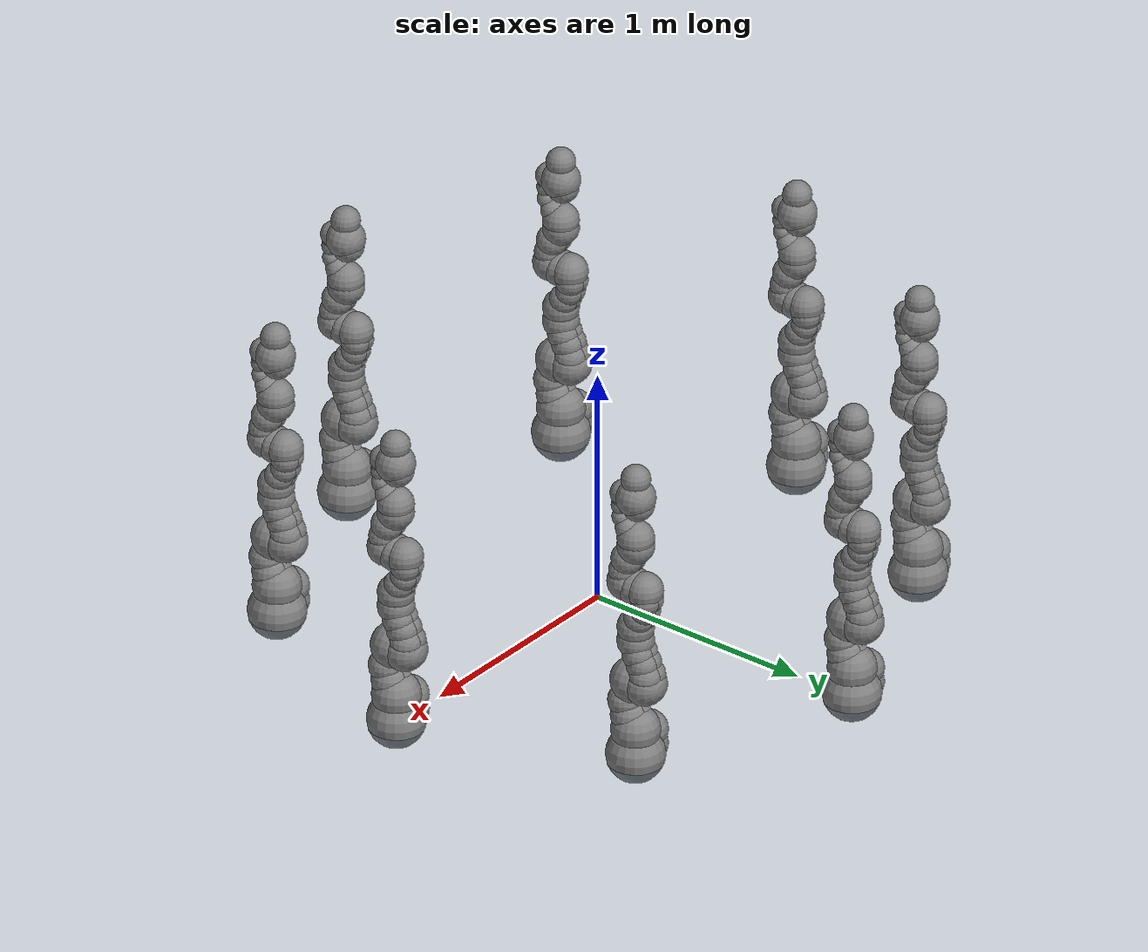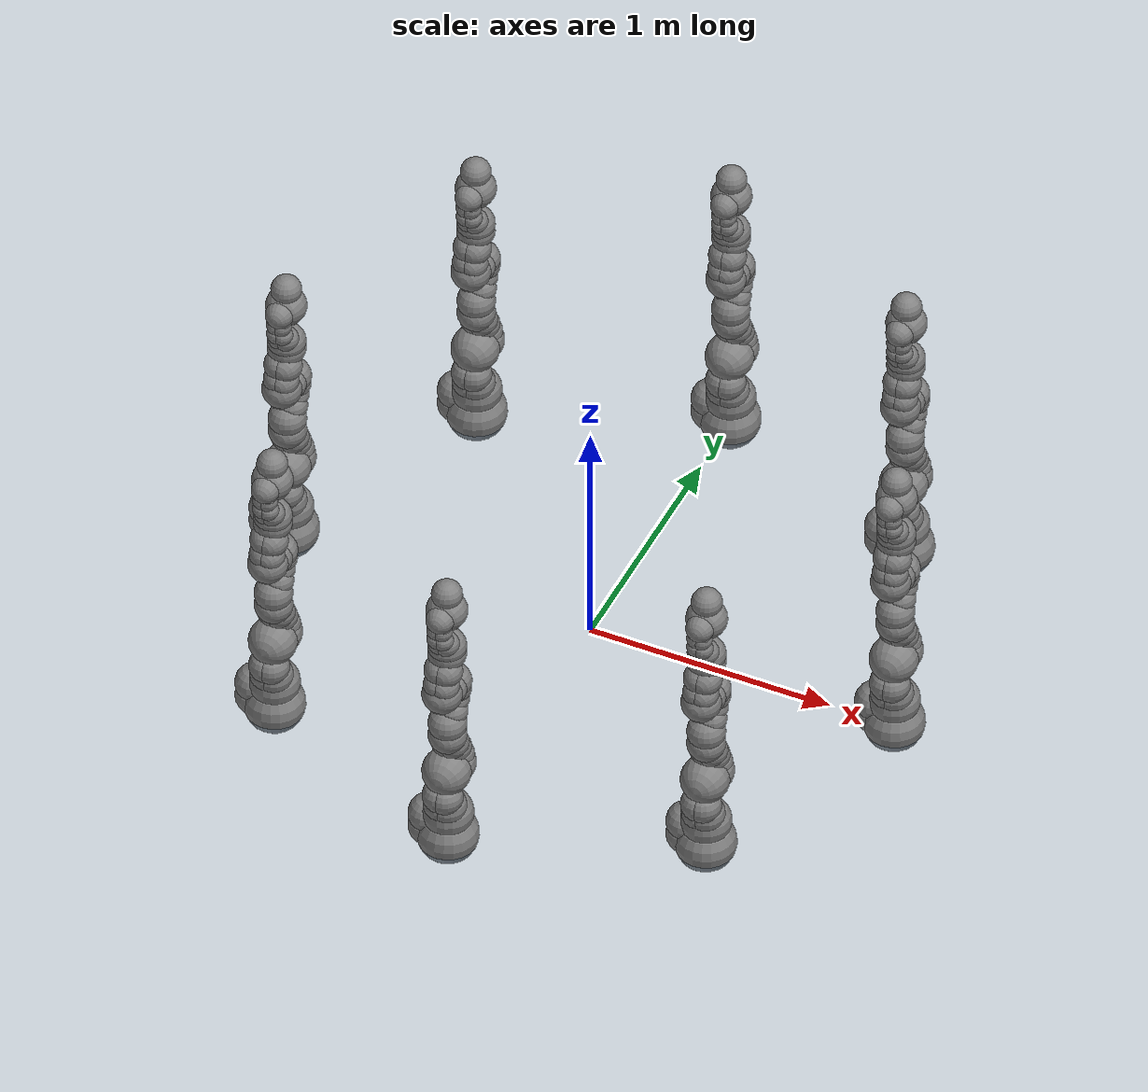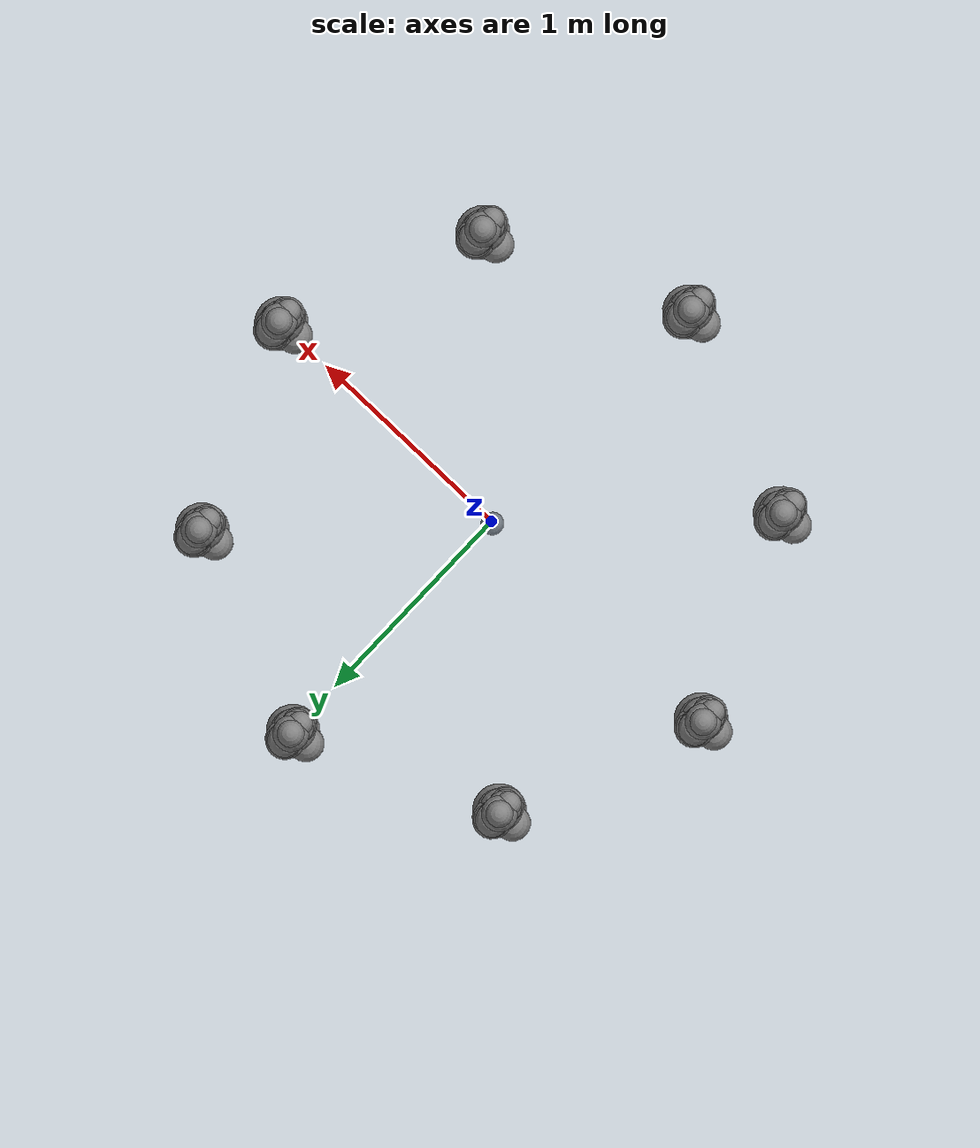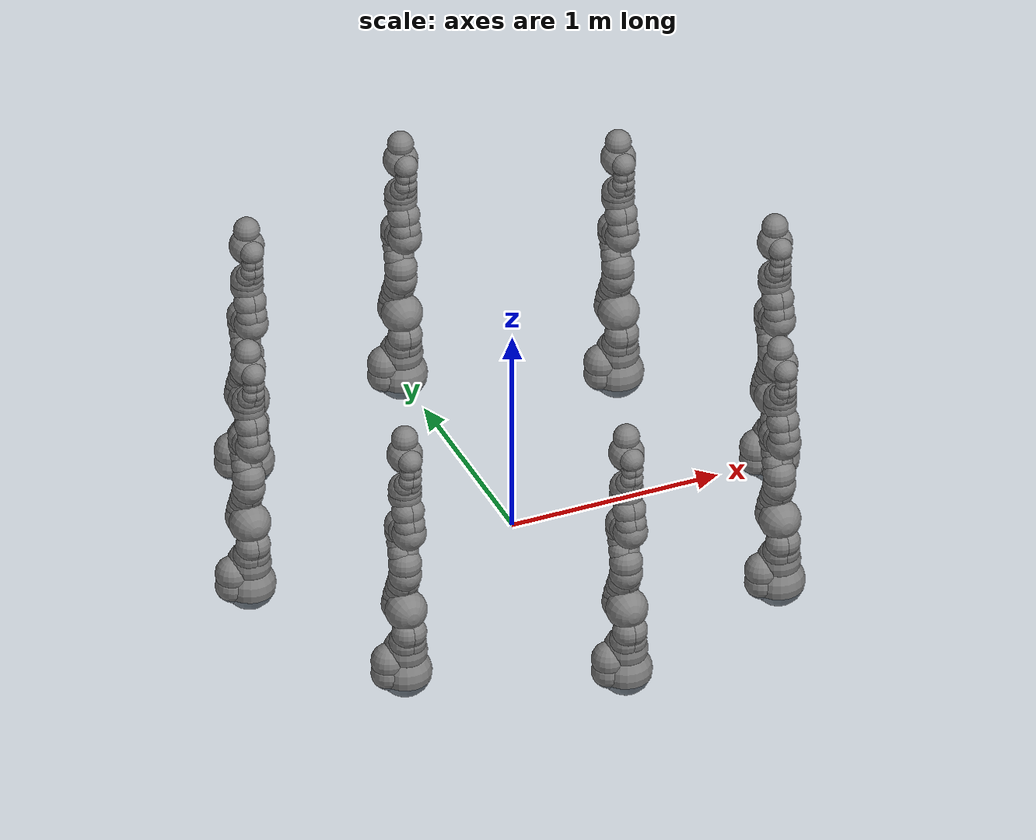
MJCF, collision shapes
<mujoco model="iiwa14 scene">
  <compiler angle="radian" meshdir="assets" autolimits="true"/>

  <option gravity="0 0 0"/>

  <default>
    <default class="iiwa">
      <material specular="0.5" shininess="0.25"/>
      <joint axis="0 0 1"/>
      <general gaintype="fixed" biastype="affine" gainprm="2000" biasprm="0 -2000 -200"/>
      <default class="joint1">
        <default class="joint2">
        </default>
      </default>
      <default class="joint3">
      </default>
      <default class="visual">
        <geom type="mesh" contype="0" conaffinity="0" group="2" material="gray"/>
      </default>
      <default class="collision">
        <geom group="3"/>
      </default>
    </default>

    <default class="iiwa_shade">
      <material specular="0.5" shininess="0.25"/>
      <joint axis="0 0 1"/>
      <general gaintype="fixed" biastype="affine" gainprm="2000" biasprm="0 -2000 -200"/>
      <default class="joint1_shade">
        <default class="joint2_shade">
        </default>
      </default>
      <default class="joint3_shade">
      </default>
      <default class="visual_shade">
        <geom type="mesh" contype="0" conaffinity="0" group="2" material="gray_shade"/>
      </default>
      <default class="collision_shade">
        <geom contype="0" conaffinity="0" group="3"/>
      </default>
    </default>
  </default>

  <asset>
    <material class="iiwa" name="gray" rgba="0.4 0.4 0.4 1"/>
    <material class="iiwa" name="light_gray" rgba="0.6 0.6 0.6 1"/>
    <material class="iiwa" name="black" rgba="0 0 0 1"/>
    <material class="iiwa" name="orange" rgba="1 0.423529 0.0392157 1"/>

    <material class="iiwa_shade" name="gray_shade" rgba="0.4 0.7 0.4 0.0000"/>
    <material class="iiwa_shade" name="light_gray_shade" rgba="0.6 0.9 0.6 0.0000"/>
    <material class="iiwa_shade" name="black_shade" rgba="0 0.3 0 0.0000"/>
    <material class="iiwa_shade" name="orange_shade" rgba="1 0.723529 0.0392157 0.0000"/>

    <mesh file="link_0.obj"/>
    <mesh file="link_1.obj"/>
    <mesh file="link_2_orange.obj"/>
    <mesh file="link_2_grey.obj"/>
    <mesh file="link_3.obj"/>
    <mesh file="band.obj"/>
    <mesh file="kuka.obj"/>
    <mesh file="link_4_orange.obj"/>
    <mesh file="link_4_grey.obj"/>
    <mesh file="link_5.obj"/>
    <mesh file="link_6_orange.obj"/>
    <mesh file="link_6_grey.obj"/>
    <mesh file="link_7.obj"/>

    <mesh scale="0.9 0.9 0.9" name="link_0_shade" file="link_0.obj"/>
    <mesh scale="0.9 0.9 0.9" name="link_1_shade" file="link_1.obj"/>
    <mesh scale="0.9 0.9 0.9" name="link_2_orange_shade" file="link_2_orange.obj"/>
    <mesh scale="0.9 0.9 0.9" name="link_2_grey_shade" file="link_2_grey.obj"/>
    <mesh scale="0.9 0.9 0.9" name="link_3_shade" file="link_3.obj"/>
    <mesh scale="0.9 0.9 0.9" name="band_shade" file="band.obj"/>
    <mesh scale="0.9 0.9 0.9" name="kuka_shade" file="kuka.obj"/>
    <mesh scale="0.9 0.9 0.9" name="link_4_orange_shade" file="link_4_orange.obj"/>
    <mesh scale="0.9 0.9 0.9" name="link_4_grey_shade" file="link_4_grey.obj"/>
    <mesh scale="0.9 0.9 0.9" name="link_5_shade" file="link_5.obj"/>
    <mesh scale="0.9 0.9 0.9" name="link_6_orange_shade" file="link_6_orange.obj"/>
    <mesh scale="0.9 0.9 0.9" name="link_6_grey_shade" file="link_6_grey.obj"/>
    <mesh scale="0.9 0.9 0.9" name="link_7_shade" file="link_7.obj"/>
  </asset>

  <statistic center="0.2 0 0.2" extent="1.0"/>

  <visual>
    <headlight diffuse="0.6 0.6 0.6" ambient="0.3 0.3 0.3" specular="0 0 0"/>
    <rgba haze="0.15 0.25 0.35 1"/>
    <global azimuth="-120" elevation="-20"/>
  </visual>

  <asset>
    <texture type="skybox" builtin="gradient" rgb1="0.3 0.5 0.7" rgb2="0 0 0" width="512" height="3072"/>
    <texture type="2d" name="groundplane" builtin="checker" mark="edge" rgb1="0.4 0.5 0.6" rgb2="0.3 0.4 0.5"
      markrgb="0.8 0.8 0.8" width="300" height="300"/>
    <material name="groundplane" texture="groundplane" texuniform="true" texrepeat="5 5" reflectance="0.2"/>
  </asset>

  <worldbody>

    <body name="model_instance_0" pos="-0.90 -0.90 0" euler="0 0 0">
      <body name="base_0" childclass="iiwa">
        <geom class="visual" mesh="link_0"/>
        <geom class="collision" size="0.12" pos="0 0 0.03"/>
        <geom class="collision" size="0.08" pos="-0.08 0 0.103"/>
        <geom class="collision" size="0.08" pos="-0.08 0 0.04"/>
        <geom class="collision" size="0.1" pos="0 0 0.14"/>
        <body name="link1_0" pos="0 0 0.1575">
          <joint name="joint1_0" class="joint1"/>
          <geom class="visual" mesh="link_1"/>
          <geom class="collision" size="0.08" pos="0 0 -0.0005"/>
          <geom class="collision" size="0.075" pos="0.01 -0.025 0.0425"/>
          <geom class="collision" size="0.075" pos="-0.01 -0.025 0.0425"/>
          <geom class="collision" size="0.07" pos="0.01 -0.045 0.1025"/>
          <geom class="collision" size="0.07" pos="-0.01 -0.045 0.1025"/>
          <body name="link2_0" pos="0 0 0.2025" quat="0 0 1 1">
            <joint name="joint2_0" class="joint2"/>
            <geom class="visual" material="orange" mesh="link_2_orange"/>
            <geom class="visual" mesh="link_2_grey"/>
            <geom class="collision" size="0.095" pos="0 0 -0.01"/>
            <geom class="collision" size="0.09" pos="0 0 0.045"/>
            <geom class="collision" size="0.07" pos="-0.01 0.04 0.054"/>
            <geom class="collision" size="0.065" pos="-0.01 0.09 0.04"/>
            <geom class="collision" size="0.065" pos="-0.01 0.13 0.02"/>
            <geom class="collision" size="0.07" pos="0.01 0.04 0.054"/>
            <geom class="collision" size="0.065" pos="0.01 0.09 0.04"/>
            <geom class="collision" size="0.065" pos="0.01 0.13 0.02"/>
            <geom class="collision" size="0.075" pos="0 0.18 0"/>
            <body name="link3_0" pos="0 0.2045 0" quat="0 0 1 1">
              <joint name="joint3_0" class="joint1"/>
              <geom class="visual" mesh="link_3"/>
              <geom class="visual" material="light_gray" mesh="band"/>
              <geom class="visual" material="black" mesh="kuka"/>
              <geom class="collision" size="0.075" pos="0 0 0.0355"/>
              <geom class="collision" size="0.06" pos="0.01 0.023 0.0855"/>
              <geom class="collision" size="0.055" pos="0.01 0.048 0.1255"/>
              <geom class="collision" size="0.06" pos="0.01 0.056 0.1755"/>
              <geom class="collision" size="0.06" pos="-0.01 0.023 0.0855"/>
              <geom class="collision" size="0.055" pos="-0.01 0.048 0.1255"/>
              <geom class="collision" size="0.06" pos="-0.01 0.056 0.1755"/>
              <geom class="collision" size="0.075" pos="0 0.045 0.2155"/>
              <geom class="collision" size="0.075" pos="0 0 0.2155"/>
              <body name="link4_0" pos="0 0 0.2155" quat="1 1 0 0">
                <joint name="joint4_0" class="joint2"/>
                <geom class="visual" material="orange" mesh="link_4_orange"/>
                <geom class="visual" mesh="link_4_grey"/>
                <geom class="collision" size="0.078" pos="0 0.01 0.046"/>
                <geom class="collision" size="0.06" pos="0.01 0.06 0.052"/>
                <geom class="collision" size="0.065" pos="0.01 0.12 0.034"/>
                <geom class="collision" size="0.06" pos="-0.01 0.06 0.052"/>
                <geom class="collision" size="0.065" pos="-0.01 0.12 0.034"/>
                <geom class="collision" size="0.075" pos="0 0.184 0"/>
                <body name="link5_0" pos="0 0.1845 0" quat="0 0 1 1">
                  <joint name="joint5_0" class="joint1"/>
                  <geom class="visual" mesh="link_5"/>
                  <geom class="visual" material="light_gray" mesh="band"/>
                  <geom class="visual" material="black" mesh="kuka"/>
                  <geom class="collision" size="0.075" pos="0 0 0.0335"/>
                  <geom class="collision" size="0.05" pos="-0.012 0.031 0.0755"/>
                  <geom class="collision" size="0.05" pos="0.012 0.031 0.0755"/>
                  <geom class="collision" size="0.04" pos="-0.012 0.06 0.1155"/>
                  <geom class="collision" size="0.04" pos="0.012 0.06 0.1155"/>
                  <geom class="collision" size="0.04" pos="-0.01 0.065 0.1655"/>
                  <geom class="collision" size="0.04" pos="0.01 0.065 0.1655"/>
                  <geom class="collision" size="0.035" pos="-0.012 0.065 0.1855"/>
                  <geom class="collision" size="0.035" pos="0.012 0.065 0.1855"/>
                  <body name="link6_0" pos="0 0 0.2155" quat="1 1 0 0">
                    <joint name="joint6_0" class="joint2"/>
                    <geom class="visual" material="orange" mesh="link_6_orange"/>
                    <geom class="visual" mesh="link_6_grey"/>
                    <geom class="collision" size="0.055" pos="0 0 -0.059"/>
                    <geom class="collision" size="0.065" pos="0 -0.03 0.011"/>
                    <geom class="collision" size="0.08"/>
                    <body name="link7_0" pos="0 0.081 0" quat="0 0 1 1">
                      <joint name="joint7_0" class="joint3"/>
                      <geom class="visual" mesh="link_7"/>
                      <geom class="collision" size="0.06" pos="0 0 0.001"/>
                    </body>
                  </body>
                </body>
              </body>
            </body>
          </body>
        </body>
      </body>
    </body>

    <body name="model_instance_1" pos=" 0.90 -0.90 0" euler="0 0 0">
      <body name="base_1" childclass="iiwa">
        <geom class="visual" mesh="link_0"/>
        <geom class="collision" size="0.12" pos="0 0 0.03"/>
        <geom class="collision" size="0.08" pos="-0.08 0 0.103"/>
        <geom class="collision" size="0.08" pos="-0.08 0 0.04"/>
        <geom class="collision" size="0.1" pos="0 0 0.14"/>
        <body name="link1_1" pos="0 0 0.1575">
          <joint name="joint1_1" class="joint1"/>
          <geom class="visual" mesh="link_1"/>
          <geom class="collision" size="0.08" pos="0 0 -0.0005"/>
          <geom class="collision" size="0.075" pos="0.01 -0.025 0.0425"/>
          <geom class="collision" size="0.075" pos="-0.01 -0.025 0.0425"/>
          <geom class="collision" size="0.07" pos="0.01 -0.045 0.1025"/>
          <geom class="collision" size="0.07" pos="-0.01 -0.045 0.1025"/>
          <body name="link2_1" pos="0 0 0.2025" quat="0 0 1 1">
            <joint name="joint2_1" class="joint2"/>
            <geom class="visual" material="orange" mesh="link_2_orange"/>
            <geom class="visual" mesh="link_2_grey"/>
            <geom class="collision" size="0.095" pos="0 0 -0.01"/>
            <geom class="collision" size="0.09" pos="0 0 0.045"/>
            <geom class="collision" size="0.07" pos="-0.01 0.04 0.054"/>
            <geom class="collision" size="0.065" pos="-0.01 0.09 0.04"/>
            <geom class="collision" size="0.065" pos="-0.01 0.13 0.02"/>
            <geom class="collision" size="0.07" pos="0.01 0.04 0.054"/>
            <geom class="collision" size="0.065" pos="0.01 0.09 0.04"/>
            <geom class="collision" size="0.065" pos="0.01 0.13 0.02"/>
            <geom class="collision" size="0.075" pos="0 0.18 0"/>
            <body name="link3_1" pos="0 0.2045 0" quat="0 0 1 1">
              <joint name="joint3_1" class="joint1"/>
              <geom class="visual" mesh="link_3"/>
              <geom class="visual" material="light_gray" mesh="band"/>
              <geom class="visual" material="black" mesh="kuka"/>
              <geom class="collision" size="0.075" pos="0 0 0.0355"/>
              <geom class="collision" size="0.06" pos="0.01 0.023 0.0855"/>
              <geom class="collision" size="0.055" pos="0.01 0.048 0.1255"/>
              <geom class="collision" size="0.06" pos="0.01 0.056 0.1755"/>
              <geom class="collision" size="0.06" pos="-0.01 0.023 0.0855"/>
              <geom class="collision" size="0.055" pos="-0.01 0.048 0.1255"/>
              <geom class="collision" size="0.06" pos="-0.01 0.056 0.1755"/>
              <geom class="collision" size="0.075" pos="0 0.045 0.2155"/>
              <geom class="collision" size="0.075" pos="0 0 0.2155"/>
              <body name="link4_1" pos="0 0 0.2155" quat="1 1 0 0">
                <joint name="joint4_1" class="joint2"/>
                <geom class="visual" material="orange" mesh="link_4_orange"/>
                <geom class="visual" mesh="link_4_grey"/>
                <geom class="collision" size="0.078" pos="0 0.01 0.046"/>
                <geom class="collision" size="0.06" pos="0.01 0.06 0.052"/>
                <geom class="collision" size="0.065" pos="0.01 0.12 0.034"/>
                <geom class="collision" size="0.06" pos="-0.01 0.06 0.052"/>
                <geom class="collision" size="0.065" pos="-0.01 0.12 0.034"/>
                <geom class="collision" size="0.075" pos="0 0.184 0"/>
                <body name="link5_1" pos="0 0.1845 0" quat="0 0 1 1">
                  <joint name="joint5_1" class="joint1"/>
                  <geom class="visual" mesh="link_5"/>
                  <geom class="visual" material="light_gray" mesh="band"/>
                  <geom class="visual" material="black" mesh="kuka"/>
                  <geom class="collision" size="0.075" pos="0 0 0.0335"/>
                  <geom class="collision" size="0.05" pos="-0.012 0.031 0.0755"/>
                  <geom class="collision" size="0.05" pos="0.012 0.031 0.0755"/>
                  <geom class="collision" size="0.04" pos="-0.012 0.06 0.1155"/>
                  <geom class="collision" size="0.04" pos="0.012 0.06 0.1155"/>
                  <geom class="collision" size="0.04" pos="-0.01 0.065 0.1655"/>
                  <geom class="collision" size="0.04" pos="0.01 0.065 0.1655"/>
                  <geom class="collision" size="0.035" pos="-0.012 0.065 0.1855"/>
                  <geom class="collision" size="0.035" pos="0.012 0.065 0.1855"/>
                  <body name="link6_1" pos="0 0 0.2155" quat="1 1 0 0">
                    <joint name="joint6_1" class="joint2"/>
                    <geom class="visual" material="orange" mesh="link_6_orange"/>
                    <geom class="visual" mesh="link_6_grey"/>
                    <geom class="collision" size="0.055" pos="0 0 -0.059"/>
                    <geom class="collision" size="0.065" pos="0 -0.03 0.011"/>
                    <geom class="collision" size="0.08"/>
                    <body name="link7_1" pos="0 0.081 0" quat="0 0 1 1">
                      <joint name="joint7_1" class="joint3"/>
                      <geom class="visual" mesh="link_7"/>
                      <geom class="collision" size="0.06" pos="0 0 0.001"/>
                    </body>
                  </body>
                </body>
              </body>
            </body>
          </body>
        </body>
      </body>
    </body>

    <body name="model_instance_2" pos=" 0.90  0.90 0" euler="0 0 0">
      <body name="base_2" childclass="iiwa">
        <geom class="visual" mesh="link_0"/>
        <geom class="collision" size="0.12" pos="0 0 0.03"/>
        <geom class="collision" size="0.08" pos="-0.08 0 0.103"/>
        <geom class="collision" size="0.08" pos="-0.08 0 0.04"/>
        <geom class="collision" size="0.1" pos="0 0 0.14"/>
        <body name="link1_2" pos="0 0 0.1575">
          <joint name="joint1_2" class="joint1"/>
          <geom class="visual" mesh="link_1"/>
          <geom class="collision" size="0.08" pos="0 0 -0.0005"/>
          <geom class="collision" size="0.075" pos="0.01 -0.025 0.0425"/>
          <geom class="collision" size="0.075" pos="-0.01 -0.025 0.0425"/>
          <geom class="collision" size="0.07" pos="0.01 -0.045 0.1025"/>
          <geom class="collision" size="0.07" pos="-0.01 -0.045 0.1025"/>
          <body name="link2_2" pos="0 0 0.2025" quat="0 0 1 1">
            <joint name="joint2_2" class="joint2"/>
            <geom class="visual" material="orange" mesh="link_2_orange"/>
            <geom class="visual" mesh="link_2_grey"/>
            <geom class="collision" size="0.095" pos="0 0 -0.01"/>
            <geom class="collision" size="0.09" pos="0 0 0.045"/>
            <geom class="collision" size="0.07" pos="-0.01 0.04 0.054"/>
            <geom class="collision" size="0.065" pos="-0.01 0.09 0.04"/>
            <geom class="collision" size="0.065" pos="-0.01 0.13 0.02"/>
            <geom class="collision" size="0.07" pos="0.01 0.04 0.054"/>
            <geom class="collision" size="0.065" pos="0.01 0.09 0.04"/>
            <geom class="collision" size="0.065" pos="0.01 0.13 0.02"/>
            <geom class="collision" size="0.075" pos="0 0.18 0"/>
            <body name="link3_2" pos="0 0.2045 0" quat="0 0 1 1">
              <joint name="joint3_2" class="joint1"/>
              <geom class="visual" mesh="link_3"/>
              <geom class="visual" material="light_gray" mesh="band"/>
              <geom class="visual" material="black" mesh="kuka"/>
              <geom class="collision" size="0.075" pos="0 0 0.0355"/>
              <geom class="collision" size="0.06" pos="0.01 0.023 0.0855"/>
              <geom class="collision" size="0.055" pos="0.01 0.048 0.1255"/>
              <geom class="collision" size="0.06" pos="0.01 0.056 0.1755"/>
              <geom class="collision" size="0.06" pos="-0.01 0.023 0.0855"/>
              <geom class="collision" size="0.055" pos="-0.01 0.048 0.1255"/>
              <geom class="collision" size="0.06" pos="-0.01 0.056 0.1755"/>
              <geom class="collision" size="0.075" pos="0 0.045 0.2155"/>
              <geom class="collision" size="0.075" pos="0 0 0.2155"/>
              <body name="link4_2" pos="0 0 0.2155" quat="1 1 0 0">
                <joint name="joint4_2" class="joint2"/>
                <geom class="visual" material="orange" mesh="link_4_orange"/>
                <geom class="visual" mesh="link_4_grey"/>
                <geom class="collision" size="0.078" pos="0 0.01 0.046"/>
                <geom class="collision" size="0.06" pos="0.01 0.06 0.052"/>
                <geom class="collision" size="0.065" pos="0.01 0.12 0.034"/>
                <geom class="collision" size="0.06" pos="-0.01 0.06 0.052"/>
                <geom class="collision" size="0.065" pos="-0.01 0.12 0.034"/>
                <geom class="collision" size="0.075" pos="0 0.184 0"/>
                <body name="link5_2" pos="0 0.1845 0" quat="0 0 1 1">
                  <joint name="joint5_2" class="joint1"/>
                  <geom class="visual" mesh="link_5"/>
                  <geom class="visual" material="light_gray" mesh="band"/>
                  <geom class="visual" material="black" mesh="kuka"/>
                  <geom class="collision" size="0.075" pos="0 0 0.0335"/>
                  <geom class="collision" size="0.05" pos="-0.012 0.031 0.0755"/>
                  <geom class="collision" size="0.05" pos="0.012 0.031 0.0755"/>
                  <geom class="collision" size="0.04" pos="-0.012 0.06 0.1155"/>
                  <geom class="collision" size="0.04" pos="0.012 0.06 0.1155"/>
                  <geom class="collision" size="0.04" pos="-0.01 0.065 0.1655"/>
                  <geom class="collision" size="0.04" pos="0.01 0.065 0.1655"/>
                  <geom class="collision" size="0.035" pos="-0.012 0.065 0.1855"/>
                  <geom class="collision" size="0.035" pos="0.012 0.065 0.1855"/>
                  <body name="link6_2" pos="0 0 0.2155" quat="1 1 0 0">
                    <joint name="joint6_2" class="joint2"/>
                    <geom class="visual" material="orange" mesh="link_6_orange"/>
                    <geom class="visual" mesh="link_6_grey"/>
                    <geom class="collision" size="0.055" pos="0 0 -0.059"/>
                    <geom class="collision" size="0.065" pos="0 -0.03 0.011"/>
                    <geom class="collision" size="0.08"/>
                    <body name="link7_2" pos="0 0.081 0" quat="0 0 1 1">
                      <joint name="joint7_2" class="joint3"/>
                      <geom class="visual" mesh="link_7"/>
                      <geom class="collision" size="0.06" pos="0 0 0.001"/>
                    </body>
                  </body>
                </body>
              </body>
            </body>
          </body>
        </body>
      </body>
    </body>

    <body name="model_instance_3" pos="-0.90  0.90 0" euler="0 0 0">
      <body name="base_3" childclass="iiwa">
        <geom class="visual" mesh="link_0"/>
        <geom class="collision" size="0.12" pos="0 0 0.03"/>
        <geom class="collision" size="0.08" pos="-0.08 0 0.103"/>
        <geom class="collision" size="0.08" pos="-0.08 0 0.04"/>
        <geom class="collision" size="0.1" pos="0 0 0.14"/>
        <body name="link1_3" pos="0 0 0.1575">
          <joint name="joint1_3" class="joint1"/>
          <geom class="visual" mesh="link_1"/>
          <geom class="collision" size="0.08" pos="0 0 -0.0005"/>
          <geom class="collision" size="0.075" pos="0.01 -0.025 0.0425"/>
          <geom class="collision" size="0.075" pos="-0.01 -0.025 0.0425"/>
          <geom class="collision" size="0.07" pos="0.01 -0.045 0.1025"/>
          <geom class="collision" size="0.07" pos="-0.01 -0.045 0.1025"/>
          <body name="link2_3" pos="0 0 0.2025" quat="0 0 1 1">
            <joint name="joint2_3" class="joint2"/>
            <geom class="visual" material="orange" mesh="link_2_orange"/>
            <geom class="visual" mesh="link_2_grey"/>
            <geom class="collision" size="0.095" pos="0 0 -0.01"/>
            <geom class="collision" size="0.09" pos="0 0 0.045"/>
            <geom class="collision" size="0.07" pos="-0.01 0.04 0.054"/>
            <geom class="collision" size="0.065" pos="-0.01 0.09 0.04"/>
            <geom class="collision" size="0.065" pos="-0.01 0.13 0.02"/>
            <geom class="collision" size="0.07" pos="0.01 0.04 0.054"/>
            <geom class="collision" size="0.065" pos="0.01 0.09 0.04"/>
            <geom class="collision" size="0.065" pos="0.01 0.13 0.02"/>
            <geom class="collision" size="0.075" pos="0 0.18 0"/>
            <body name="link3_3" pos="0 0.2045 0" quat="0 0 1 1">
              <joint name="joint3_3" class="joint1"/>
              <geom class="visual" mesh="link_3"/>
              <geom class="visual" material="light_gray" mesh="band"/>
              <geom class="visual" material="black" mesh="kuka"/>
              <geom class="collision" size="0.075" pos="0 0 0.0355"/>
              <geom class="collision" size="0.06" pos="0.01 0.023 0.0855"/>
              <geom class="collision" size="0.055" pos="0.01 0.048 0.1255"/>
              <geom class="collision" size="0.06" pos="0.01 0.056 0.1755"/>
              <geom class="collision" size="0.06" pos="-0.01 0.023 0.0855"/>
              <geom class="collision" size="0.055" pos="-0.01 0.048 0.1255"/>
              <geom class="collision" size="0.06" pos="-0.01 0.056 0.1755"/>
              <geom class="collision" size="0.075" pos="0 0.045 0.2155"/>
              <geom class="collision" size="0.075" pos="0 0 0.2155"/>
              <body name="link4_3" pos="0 0 0.2155" quat="1 1 0 0">
                <joint name="joint4_3" class="joint2"/>
                <geom class="visual" material="orange" mesh="link_4_orange"/>
                <geom class="visual" mesh="link_4_grey"/>
                <geom class="collision" size="0.078" pos="0 0.01 0.046"/>
                <geom class="collision" size="0.06" pos="0.01 0.06 0.052"/>
                <geom class="collision" size="0.065" pos="0.01 0.12 0.034"/>
                <geom class="collision" size="0.06" pos="-0.01 0.06 0.052"/>
                <geom class="collision" size="0.065" pos="-0.01 0.12 0.034"/>
                <geom class="collision" size="0.075" pos="0 0.184 0"/>
                <body name="link5_3" pos="0 0.1845 0" quat="0 0 1 1">
                  <joint name="joint5_3" class="joint1"/>
                  <geom class="visual" mesh="link_5"/>
                  <geom class="visual" material="light_gray" mesh="band"/>
                  <geom class="visual" material="black" mesh="kuka"/>
                  <geom class="collision" size="0.075" pos="0 0 0.0335"/>
                  <geom class="collision" size="0.05" pos="-0.012 0.031 0.0755"/>
                  <geom class="collision" size="0.05" pos="0.012 0.031 0.0755"/>
                  <geom class="collision" size="0.04" pos="-0.012 0.06 0.1155"/>
                  <geom class="collision" size="0.04" pos="0.012 0.06 0.1155"/>
                  <geom class="collision" size="0.04" pos="-0.01 0.065 0.1655"/>
                  <geom class="collision" size="0.04" pos="0.01 0.065 0.1655"/>
                  <geom class="collision" size="0.035" pos="-0.012 0.065 0.1855"/>
                  <geom class="collision" size="0.035" pos="0.012 0.065 0.1855"/>
                  <body name="link6_3" pos="0 0 0.2155" quat="1 1 0 0">
                    <joint name="joint6_3" class="joint2"/>
                    <geom class="visual" material="orange" mesh="link_6_orange"/>
                    <geom class="visual" mesh="link_6_grey"/>
                    <geom class="collision" size="0.055" pos="0 0 -0.059"/>
                    <geom class="collision" size="0.065" pos="0 -0.03 0.011"/>
                    <geom class="collision" size="0.08"/>
                    <body name="link7_3" pos="0 0.081 0" quat="0 0 1 1">
                      <joint name="joint7_3" class="joint3"/>
                      <geom class="visual" mesh="link_7"/>
                      <geom class="collision" size="0.06" pos="0 0 0.001"/>
                    </body>
                  </body>
                </body>
              </body>
            </body>
          </body>
        </body>
      </body>
    </body>

    <body name="model_instance_4" pos=" 0.0  1.27 0" euler="0 0 0">
      <body name="base_4" childclass="iiwa">
        <geom class="visual" mesh="link_0"/>
        <geom class="collision" size="0.12" pos="0 0 0.03"/>
        <geom class="collision" size="0.08" pos="-0.08 0 0.103"/>
        <geom class="collision" size="0.08" pos="-0.08 0 0.04"/>
        <geom class="collision" size="0.1" pos="0 0 0.14"/>
        <body name="link1_4" pos="0 0 0.1575">
          <joint name="joint1_4" class="joint1"/>
          <geom class="visual" mesh="link_1"/>
          <geom class="collision" size="0.08" pos="0 0 -0.0005"/>
          <geom class="collision" size="0.075" pos="0.01 -0.025 0.0425"/>
          <geom class="collision" size="0.075" pos="-0.01 -0.025 0.0425"/>
          <geom class="collision" size="0.07" pos="0.01 -0.045 0.1025"/>
          <geom class="collision" size="0.07" pos="-0.01 -0.045 0.1025"/>
          <body name="link2_4" pos="0 0 0.2025" quat="0 0 1 1">
            <joint name="joint2_4" class="joint2"/>
            <geom class="visual" material="orange" mesh="link_2_orange"/>
            <geom class="visual" mesh="link_2_grey"/>
            <geom class="collision" size="0.095" pos="0 0 -0.01"/>
            <geom class="collision" size="0.09" pos="0 0 0.045"/>
            <geom class="collision" size="0.07" pos="-0.01 0.04 0.054"/>
            <geom class="collision" size="0.065" pos="-0.01 0.09 0.04"/>
            <geom class="collision" size="0.065" pos="-0.01 0.13 0.02"/>
            <geom class="collision" size="0.07" pos="0.01 0.04 0.054"/>
            <geom class="collision" size="0.065" pos="0.01 0.09 0.04"/>
            <geom class="collision" size="0.065" pos="0.01 0.13 0.02"/>
            <geom class="collision" size="0.075" pos="0 0.18 0"/>
            <body name="link3_4" pos="0 0.2045 0" quat="0 0 1 1">
              <joint name="joint3_4" class="joint1"/>
              <geom class="visual" mesh="link_3"/>
              <geom class="visual" material="light_gray" mesh="band"/>
              <geom class="visual" material="black" mesh="kuka"/>
              <geom class="collision" size="0.075" pos="0 0 0.0355"/>
              <geom class="collision" size="0.06" pos="0.01 0.023 0.0855"/>
              <geom class="collision" size="0.055" pos="0.01 0.048 0.1255"/>
              <geom class="collision" size="0.06" pos="0.01 0.056 0.1755"/>
              <geom class="collision" size="0.06" pos="-0.01 0.023 0.0855"/>
              <geom class="collision" size="0.055" pos="-0.01 0.048 0.1255"/>
              <geom class="collision" size="0.06" pos="-0.01 0.056 0.1755"/>
              <geom class="collision" size="0.075" pos="0 0.045 0.2155"/>
              <geom class="collision" size="0.075" pos="0 0 0.2155"/>
              <body name="link4_4" pos="0 0 0.2155" quat="1 1 0 0">
                <joint name="joint4_4" class="joint2"/>
                <geom class="visual" material="orange" mesh="link_4_orange"/>
                <geom class="visual" mesh="link_4_grey"/>
                <geom class="collision" size="0.078" pos="0 0.01 0.046"/>
                <geom class="collision" size="0.06" pos="0.01 0.06 0.052"/>
                <geom class="collision" size="0.065" pos="0.01 0.12 0.034"/>
                <geom class="collision" size="0.06" pos="-0.01 0.06 0.052"/>
                <geom class="collision" size="0.065" pos="-0.01 0.12 0.034"/>
                <geom class="collision" size="0.075" pos="0 0.184 0"/>
                <body name="link5_4" pos="0 0.1845 0" quat="0 0 1 1">
                  <joint name="joint5_4" class="joint1"/>
                  <geom class="visual" mesh="link_5"/>
                  <geom class="visual" material="light_gray" mesh="band"/>
                  <geom class="visual" material="black" mesh="kuka"/>
                  <geom class="collision" size="0.075" pos="0 0 0.0335"/>
                  <geom class="collision" size="0.05" pos="-0.012 0.031 0.0755"/>
                  <geom class="collision" size="0.05" pos="0.012 0.031 0.0755"/>
                  <geom class="collision" size="0.04" pos="-0.012 0.06 0.1155"/>
                  <geom class="collision" size="0.04" pos="0.012 0.06 0.1155"/>
                  <geom class="collision" size="0.04" pos="-0.01 0.065 0.1655"/>
                  <geom class="collision" size="0.04" pos="0.01 0.065 0.1655"/>
                  <geom class="collision" size="0.035" pos="-0.012 0.065 0.1855"/>
                  <geom class="collision" size="0.035" pos="0.012 0.065 0.1855"/>
                  <body name="link6_4" pos="0 0 0.2155" quat="1 1 0 0">
                    <joint name="joint6_4" class="joint2"/>
                    <geom class="visual" material="orange" mesh="link_6_orange"/>
                    <geom class="visual" mesh="link_6_grey"/>
                    <geom class="collision" size="0.055" pos="0 0 -0.059"/>
                    <geom class="collision" size="0.065" pos="0 -0.03 0.011"/>
                    <geom class="collision" size="0.08"/>
                    <body name="link7_4" pos="0 0.081 0" quat="0 0 1 1">
                      <joint name="joint7_4" class="joint3"/>
                      <geom class="visual" mesh="link_7"/>
                      <geom class="collision" size="0.06" pos="0 0 0.001"/>
                    </body>
                  </body>
                </body>
              </body>
            </body>
          </body>
        </body>
      </body>
    </body>

    <body name="model_instance_5" pos=" 1.27  0.0 0" euler="0 0 0">
      <body name="base_5" childclass="iiwa">
        <geom class="visual" mesh="link_0"/>
        <geom class="collision" size="0.12" pos="0 0 0.03"/>
        <geom class="collision" size="0.08" pos="-0.08 0 0.103"/>
        <geom class="collision" size="0.08" pos="-0.08 0 0.04"/>
        <geom class="collision" size="0.1" pos="0 0 0.14"/>
        <body name="link1_5" pos="0 0 0.1575">
          <joint name="joint1_5" class="joint1"/>
          <geom class="visual" mesh="link_1"/>
          <geom class="collision" size="0.08" pos="0 0 -0.0005"/>
          <geom class="collision" size="0.075" pos="0.01 -0.025 0.0425"/>
          <geom class="collision" size="0.075" pos="-0.01 -0.025 0.0425"/>
          <geom class="collision" size="0.07" pos="0.01 -0.045 0.1025"/>
          <geom class="collision" size="0.07" pos="-0.01 -0.045 0.1025"/>
          <body name="link2_5" pos="0 0 0.2025" quat="0 0 1 1">
            <joint name="joint2_5" class="joint2"/>
            <geom class="visual" material="orange" mesh="link_2_orange"/>
            <geom class="visual" mesh="link_2_grey"/>
            <geom class="collision" size="0.095" pos="0 0 -0.01"/>
            <geom class="collision" size="0.09" pos="0 0 0.045"/>
            <geom class="collision" size="0.07" pos="-0.01 0.04 0.054"/>
            <geom class="collision" size="0.065" pos="-0.01 0.09 0.04"/>
            <geom class="collision" size="0.065" pos="-0.01 0.13 0.02"/>
            <geom class="collision" size="0.07" pos="0.01 0.04 0.054"/>
            <geom class="collision" size="0.065" pos="0.01 0.09 0.04"/>
            <geom class="collision" size="0.065" pos="0.01 0.13 0.02"/>
            <geom class="collision" size="0.075" pos="0 0.18 0"/>
            <body name="link3_5" pos="0 0.2045 0" quat="0 0 1 1">
              <joint name="joint3_5" class="joint1"/>
              <geom class="visual" mesh="link_3"/>
              <geom class="visual" material="light_gray" mesh="band"/>
              <geom class="visual" material="black" mesh="kuka"/>
              <geom class="collision" size="0.075" pos="0 0 0.0355"/>
              <geom class="collision" size="0.06" pos="0.01 0.023 0.0855"/>
              <geom class="collision" size="0.055" pos="0.01 0.048 0.1255"/>
              <geom class="collision" size="0.06" pos="0.01 0.056 0.1755"/>
              <geom class="collision" size="0.06" pos="-0.01 0.023 0.0855"/>
              <geom class="collision" size="0.055" pos="-0.01 0.048 0.1255"/>
              <geom class="collision" size="0.06" pos="-0.01 0.056 0.1755"/>
              <geom class="collision" size="0.075" pos="0 0.045 0.2155"/>
              <geom class="collision" size="0.075" pos="0 0 0.2155"/>
              <body name="link4_5" pos="0 0 0.2155" quat="1 1 0 0">
                <joint name="joint4_5" class="joint2"/>
                <geom class="visual" material="orange" mesh="link_4_orange"/>
                <geom class="visual" mesh="link_4_grey"/>
                <geom class="collision" size="0.078" pos="0 0.01 0.046"/>
                <geom class="collision" size="0.06" pos="0.01 0.06 0.052"/>
                <geom class="collision" size="0.065" pos="0.01 0.12 0.034"/>
                <geom class="collision" size="0.06" pos="-0.01 0.06 0.052"/>
                <geom class="collision" size="0.065" pos="-0.01 0.12 0.034"/>
                <geom class="collision" size="0.075" pos="0 0.184 0"/>
                <body name="link5_5" pos="0 0.1845 0" quat="0 0 1 1">
                  <joint name="joint5_5" class="joint1"/>
                  <geom class="visual" mesh="link_5"/>
                  <geom class="visual" material="light_gray" mesh="band"/>
                  <geom class="visual" material="black" mesh="kuka"/>
                  <geom class="collision" size="0.075" pos="0 0 0.0335"/>
                  <geom class="collision" size="0.05" pos="-0.012 0.031 0.0755"/>
                  <geom class="collision" size="0.05" pos="0.012 0.031 0.0755"/>
                  <geom class="collision" size="0.04" pos="-0.012 0.06 0.1155"/>
                  <geom class="collision" size="0.04" pos="0.012 0.06 0.1155"/>
                  <geom class="collision" size="0.04" pos="-0.01 0.065 0.1655"/>
                  <geom class="collision" size="0.04" pos="0.01 0.065 0.1655"/>
                  <geom class="collision" size="0.035" pos="-0.012 0.065 0.1855"/>
                  <geom class="collision" size="0.035" pos="0.012 0.065 0.1855"/>
                  <body name="link6_5" pos="0 0 0.2155" quat="1 1 0 0">
                    <joint name="joint6_5" class="joint2"/>
                    <geom class="visual" material="orange" mesh="link_6_orange"/>
                    <geom class="visual" mesh="link_6_grey"/>
                    <geom class="collision" size="0.055" pos="0 0 -0.059"/>
                    <geom class="collision" size="0.065" pos="0 -0.03 0.011"/>
                    <geom class="collision" size="0.08"/>
                    <body name="link7_5" pos="0 0.081 0" quat="0 0 1 1">
                      <joint name="joint7_5" class="joint3"/>
                      <geom class="visual" mesh="link_7"/>
                      <geom class="collision" size="0.06" pos="0 0 0.001"/>
                    </body>
                  </body>
                </body>
              </body>
            </body>
          </body>
        </body>
      </body>
    </body>

    <body name="model_instance_6" pos="-1.27  0.0 0" euler="0 0 0">
      <body name="base_6" childclass="iiwa">
        <geom class="visual" mesh="link_0"/>
        <geom class="collision" size="0.12" pos="0 0 0.03"/>
        <geom class="collision" size="0.08" pos="-0.08 0 0.103"/>
        <geom class="collision" size="0.08" pos="-0.08 0 0.04"/>
        <geom class="collision" size="0.1" pos="0 0 0.14"/>
        <body name="link1_6" pos="0 0 0.1575">
          <joint name="joint1_6" class="joint1"/>
          <geom class="visual" mesh="link_1"/>
          <geom class="collision" size="0.08" pos="0 0 -0.0005"/>
          <geom class="collision" size="0.075" pos="0.01 -0.025 0.0425"/>
          <geom class="collision" size="0.075" pos="-0.01 -0.025 0.0425"/>
          <geom class="collision" size="0.07" pos="0.01 -0.045 0.1025"/>
          <geom class="collision" size="0.07" pos="-0.01 -0.045 0.1025"/>
          <body name="link2_6" pos="0 0 0.2025" quat="0 0 1 1">
            <joint name="joint2_6" class="joint2"/>
            <geom class="visual" material="orange" mesh="link_2_orange"/>
            <geom class="visual" mesh="link_2_grey"/>
            <geom class="collision" size="0.095" pos="0 0 -0.01"/>
            <geom class="collision" size="0.09" pos="0 0 0.045"/>
            <geom class="collision" size="0.07" pos="-0.01 0.04 0.054"/>
            <geom class="collision" size="0.065" pos="-0.01 0.09 0.04"/>
            <geom class="collision" size="0.065" pos="-0.01 0.13 0.02"/>
            <geom class="collision" size="0.07" pos="0.01 0.04 0.054"/>
            <geom class="collision" size="0.065" pos="0.01 0.09 0.04"/>
            <geom class="collision" size="0.065" pos="0.01 0.13 0.02"/>
            <geom class="collision" size="0.075" pos="0 0.18 0"/>
            <body name="link3_6" pos="0 0.2045 0" quat="0 0 1 1">
              <joint name="joint3_6" class="joint1"/>
              <geom class="visual" mesh="link_3"/>
              <geom class="visual" material="light_gray" mesh="band"/>
              <geom class="visual" material="black" mesh="kuka"/>
              <geom class="collision" size="0.075" pos="0 0 0.0355"/>
              <geom class="collision" size="0.06" pos="0.01 0.023 0.0855"/>
              <geom class="collision" size="0.055" pos="0.01 0.048 0.1255"/>
              <geom class="collision" size="0.06" pos="0.01 0.056 0.1755"/>
              <geom class="collision" size="0.06" pos="-0.01 0.023 0.0855"/>
              <geom class="collision" size="0.055" pos="-0.01 0.048 0.1255"/>
              <geom class="collision" size="0.06" pos="-0.01 0.056 0.1755"/>
              <geom class="collision" size="0.075" pos="0 0.045 0.2155"/>
              <geom class="collision" size="0.075" pos="0 0 0.2155"/>
              <body name="link4_6" pos="0 0 0.2155" quat="1 1 0 0">
                <joint name="joint4_6" class="joint2"/>
                <geom class="visual" material="orange" mesh="link_4_orange"/>
                <geom class="visual" mesh="link_4_grey"/>
                <geom class="collision" size="0.078" pos="0 0.01 0.046"/>
                <geom class="collision" size="0.06" pos="0.01 0.06 0.052"/>
                <geom class="collision" size="0.065" pos="0.01 0.12 0.034"/>
                <geom class="collision" size="0.06" pos="-0.01 0.06 0.052"/>
                <geom class="collision" size="0.065" pos="-0.01 0.12 0.034"/>
                <geom class="collision" size="0.075" pos="0 0.184 0"/>
                <body name="link5_6" pos="0 0.1845 0" quat="0 0 1 1">
                  <joint name="joint5_6" class="joint1"/>
                  <geom class="visual" mesh="link_5"/>
                  <geom class="visual" material="light_gray" mesh="band"/>
                  <geom class="visual" material="black" mesh="kuka"/>
                  <geom class="collision" size="0.075" pos="0 0 0.0335"/>
                  <geom class="collision" size="0.05" pos="-0.012 0.031 0.0755"/>
                  <geom class="collision" size="0.05" pos="0.012 0.031 0.0755"/>
                  <geom class="collision" size="0.04" pos="-0.012 0.06 0.1155"/>
                  <geom class="collision" size="0.04" pos="0.012 0.06 0.1155"/>
                  <geom class="collision" size="0.04" pos="-0.01 0.065 0.1655"/>
                  <geom class="collision" size="0.04" pos="0.01 0.065 0.1655"/>
                  <geom class="collision" size="0.035" pos="-0.012 0.065 0.1855"/>
                  <geom class="collision" size="0.035" pos="0.012 0.065 0.1855"/>
                  <body name="link6_6" pos="0 0 0.2155" quat="1 1 0 0">
                    <joint name="joint6_6" class="joint2"/>
                    <geom class="visual" material="orange" mesh="link_6_orange"/>
                    <geom class="visual" mesh="link_6_grey"/>
                    <geom class="collision" size="0.055" pos="0 0 -0.059"/>
                    <geom class="collision" size="0.065" pos="0 -0.03 0.011"/>
                    <geom class="collision" size="0.08"/>
                    <body name="link7_6" pos="0 0.081 0" quat="0 0 1 1">
                      <joint name="joint7_6" class="joint3"/>
                      <geom class="visual" mesh="link_7"/>
                      <geom class="collision" size="0.06" pos="0 0 0.001"/>
                    </body>
                  </body>
                </body>
              </body>
            </body>
          </body>
        </body>
      </body>
    </body>

    <body name="model_instance_7" pos=" 0.0 -1.27 0" euler="0 0 0">
      <body name="base_7" childclass="iiwa">
        <geom class="visual" mesh="link_0"/>
        <geom class="collision" size="0.12" pos="0 0 0.03"/>
        <geom class="collision" size="0.08" pos="-0.08 0 0.103"/>
        <geom class="collision" size="0.08" pos="-0.08 0 0.04"/>
        <geom class="collision" size="0.1" pos="0 0 0.14"/>
        <body name="link1_7" pos="0 0 0.1575">
          <joint name="joint1_7" class="joint1"/>
          <geom class="visual" mesh="link_1"/>
          <geom class="collision" size="0.08" pos="0 0 -0.0005"/>
          <geom class="collision" size="0.075" pos="0.01 -0.025 0.0425"/>
          <geom class="collision" size="0.075" pos="-0.01 -0.025 0.0425"/>
          <geom class="collision" size="0.07" pos="0.01 -0.045 0.1025"/>
          <geom class="collision" size="0.07" pos="-0.01 -0.045 0.1025"/>
          <body name="link2_7" pos="0 0 0.2025" quat="0 0 1 1">
            <joint name="joint2_7" class="joint2"/>
            <geom class="visual" material="orange" mesh="link_2_orange"/>
            <geom class="visual" mesh="link_2_grey"/>
            <geom class="collision" size="0.095" pos="0 0 -0.01"/>
            <geom class="collision" size="0.09" pos="0 0 0.045"/>
            <geom class="collision" size="0.07" pos="-0.01 0.04 0.054"/>
            <geom class="collision" size="0.065" pos="-0.01 0.09 0.04"/>
            <geom class="collision" size="0.065" pos="-0.01 0.13 0.02"/>
            <geom class="collision" size="0.07" pos="0.01 0.04 0.054"/>
            <geom class="collision" size="0.065" pos="0.01 0.09 0.04"/>
            <geom class="collision" size="0.065" pos="0.01 0.13 0.02"/>
            <geom class="collision" size="0.075" pos="0 0.18 0"/>
            <body name="link3_7" pos="0 0.2045 0" quat="0 0 1 1">
              <joint name="joint3_7" class="joint1"/>
              <geom class="visual" mesh="link_3"/>
              <geom class="visual" material="light_gray" mesh="band"/>
              <geom class="visual" material="black" mesh="kuka"/>
              <geom class="collision" size="0.075" pos="0 0 0.0355"/>
              <geom class="collision" size="0.06" pos="0.01 0.023 0.0855"/>
              <geom class="collision" size="0.055" pos="0.01 0.048 0.1255"/>
              <geom class="collision" size="0.06" pos="0.01 0.056 0.1755"/>
              <geom class="collision" size="0.06" pos="-0.01 0.023 0.0855"/>
              <geom class="collision" size="0.055" pos="-0.01 0.048 0.1255"/>
              <geom class="collision" size="0.06" pos="-0.01 0.056 0.1755"/>
              <geom class="collision" size="0.075" pos="0 0.045 0.2155"/>
              <geom class="collision" size="0.075" pos="0 0 0.2155"/>
              <body name="link4_7" pos="0 0 0.2155" quat="1 1 0 0">
                <joint name="joint4_7" class="joint2"/>
                <geom class="visual" material="orange" mesh="link_4_orange"/>
                <geom class="visual" mesh="link_4_grey"/>
                <geom class="collision" size="0.078" pos="0 0.01 0.046"/>
                <geom class="collision" size="0.06" pos="0.01 0.06 0.052"/>
                <geom class="collision" size="0.065" pos="0.01 0.12 0.034"/>
                <geom class="collision" size="0.06" pos="-0.01 0.06 0.052"/>
                <geom class="collision" size="0.065" pos="-0.01 0.12 0.034"/>
                <geom class="collision" size="0.075" pos="0 0.184 0"/>
                <body name="link5_7" pos="0 0.1845 0" quat="0 0 1 1">
                  <joint name="joint5_7" class="joint1"/>
                  <geom class="visual" mesh="link_5"/>
                  <geom class="visual" material="light_gray" mesh="band"/>
                  <geom class="visual" material="black" mesh="kuka"/>
                  <geom class="collision" size="0.075" pos="0 0 0.0335"/>
                  <geom class="collision" size="0.05" pos="-0.012 0.031 0.0755"/>
                  <geom class="collision" size="0.05" pos="0.012 0.031 0.0755"/>
                  <geom class="collision" size="0.04" pos="-0.012 0.06 0.1155"/>
                  <geom class="collision" size="0.04" pos="0.012 0.06 0.1155"/>
                  <geom class="collision" size="0.04" pos="-0.01 0.065 0.1655"/>
                  <geom class="collision" size="0.04" pos="0.01 0.065 0.1655"/>
                  <geom class="collision" size="0.035" pos="-0.012 0.065 0.1855"/>
                  <geom class="collision" size="0.035" pos="0.012 0.065 0.1855"/>
                  <body name="link6_7" pos="0 0 0.2155" quat="1 1 0 0">
                    <joint name="joint6_7" class="joint2"/>
                    <geom class="visual" material="orange" mesh="link_6_orange"/>
                    <geom class="visual" mesh="link_6_grey"/>
                    <geom class="collision" size="0.055" pos="0 0 -0.059"/>
                    <geom class="collision" size="0.065" pos="0 -0.03 0.011"/>
                    <geom class="collision" size="0.08"/>
                    <body name="link7_7" pos="0 0.081 0" quat="0 0 1 1">
                      <joint name="joint7_7" class="joint3"/>
                      <geom class="visual" mesh="link_7"/>
                      <geom class="collision" size="0.06" pos="0 0 0.001"/>
                    </body>
                  </body>
                </body>
              </body>
            </body>
          </body>
        </body>
      </body>
    </body>

    <body name="model_shade_0" pos="-0.90 -0.90 0" euler="0 0 0">
      <body name="base_0_shade" childclass="iiwa_shade">
        <geom class="visual_shade" mesh="link_0_shade"/>
        <geom class="collision_shade" size="0.12" pos="0 0 0.03"/>
        <geom class="collision_shade" size="0.08" pos="-0.08 0 0.103"/>
        <geom class="collision_shade" size="0.08" pos="-0.08 0 0.04"/>
        <geom class="collision_shade" size="0.1" pos="0 0 0.14"/>
        <body name="link1_0_shade" pos="0 0 0.1575">
          <joint name="joint1_0_shade" class="joint1_shade"/>
          <geom class="visual_shade" mesh="link_1_shade"/>
          <geom class="collision_shade" size="0.08" pos="0 0 -0.0005"/>
          <geom class="collision_shade" size="0.075" pos="0.01 -0.025 0.0425"/>
          <geom class="collision_shade" size="0.075" pos="-0.01 -0.025 0.0425"/>
          <geom class="collision_shade" size="0.07" pos="0.01 -0.045 0.1025"/>
          <geom class="collision_shade" size="0.07" pos="-0.01 -0.045 0.1025"/>
          <body name="link2_0_shade" pos="0 0 0.2025" quat="0 0 1 1">
            <joint name="joint2_0_shade" class="joint2_shade"/>
            <geom class="visual_shade" material="orange_shade" mesh="link_2_orange_shade"/>
            <geom class="visual_shade" mesh="link_2_grey_shade"/>
            <geom class="collision_shade" size="0.095" pos="0 0 -0.01"/>
            <geom class="collision_shade" size="0.09" pos="0 0 0.045"/>
            <geom class="collision_shade" size="0.07" pos="-0.01 0.04 0.054"/>
            <geom class="collision_shade" size="0.065" pos="-0.01 0.09 0.04"/>
            <geom class="collision_shade" size="0.065" pos="-0.01 0.13 0.02"/>
            <geom class="collision_shade" size="0.07" pos="0.01 0.04 0.054"/>
            <geom class="collision_shade" size="0.065" pos="0.01 0.09 0.04"/>
            <geom class="collision_shade" size="0.065" pos="0.01 0.13 0.02"/>
            <geom class="collision_shade" size="0.075" pos="0 0.18 0"/>
            <body name="link3_0_shade" pos="0 0.2045 0" quat="0 0 1 1">
              <joint name="joint3_0_shade" class="joint1_shade"/>
              <geom class="visual_shade" mesh="link_3_shade"/>
              <geom class="visual_shade" material="light_gray_shade" mesh="band_shade"/>
              <geom class="visual_shade" material="black_shade" mesh="kuka_shade"/>
              <geom class="collision_shade" size="0.075" pos="0 0 0.0355"/>
              <geom class="collision_shade" size="0.06" pos="0.01 0.023 0.0855"/>
              <geom class="collision_shade" size="0.055" pos="0.01 0.048 0.1255"/>
              <geom class="collision_shade" size="0.06" pos="0.01 0.056 0.1755"/>
              <geom class="collision_shade" size="0.06" pos="-0.01 0.023 0.0855"/>
              <geom class="collision_shade" size="0.055" pos="-0.01 0.048 0.1255"/>
              <geom class="collision_shade" size="0.06" pos="-0.01 0.056 0.1755"/>
              <geom class="collision_shade" size="0.075" pos="0 0.045 0.2155"/>
              <geom class="collision_shade" size="0.075" pos="0 0 0.2155"/>
              <body name="link4_0_shade" pos="0 0 0.2155" quat="1 1 0 0">
                <joint name="joint4_0_shade" class="joint2_shade"/>
                <geom class="visual_shade" material="orange_shade" mesh="link_4_orange_shade"/>
                <geom class="visual_shade" mesh="link_4_grey_shade"/>
                <geom class="collision_shade" size="0.078" pos="0 0.01 0.046"/>
                <geom class="collision_shade" size="0.06" pos="0.01 0.06 0.052"/>
                <geom class="collision_shade" size="0.065" pos="0.01 0.12 0.034"/>
                <geom class="collision_shade" size="0.06" pos="-0.01 0.06 0.052"/>
                <geom class="collision_shade" size="0.065" pos="-0.01 0.12 0.034"/>
                <geom class="collision_shade" size="0.075" pos="0 0.184 0"/>
                <body name="link5_0_shade" pos="0 0.1845 0" quat="0 0 1 1">
                  <joint name="joint5_0_shade" class="joint1_shade"/>
                  <geom class="visual_shade" mesh="link_5_shade"/>
                  <geom class="visual_shade" material="light_gray_shade" mesh="band_shade"/>
                  <geom class="visual_shade" material="black_shade" mesh="kuka_shade"/>
                  <geom class="collision_shade" size="0.075" pos="0 0 0.0335"/>
                  <geom class="collision_shade" size="0.05" pos="-0.012 0.031 0.0755"/>
                  <geom class="collision_shade" size="0.05" pos="0.012 0.031 0.0755"/>
                  <geom class="collision_shade" size="0.04" pos="-0.012 0.06 0.1155"/>
                  <geom class="collision_shade" size="0.04" pos="0.012 0.06 0.1155"/>
                  <geom class="collision_shade" size="0.04" pos="-0.01 0.065 0.1655"/>
                  <geom class="collision_shade" size="0.04" pos="0.01 0.065 0.1655"/>
                  <geom class="collision_shade" size="0.035" pos="-0.012 0.065 0.1855"/>
                  <geom class="collision_shade" size="0.035" pos="0.012 0.065 0.1855"/>
                  <body name="link6_0_shade" pos="0 0 0.2155" quat="1 1 0 0">
                    <joint name="joint6_0_shade" class="joint2_shade"/>
                    <geom class="visual_shade" material="orange_shade" mesh="link_6_orange_shade"/>
                    <geom class="visual_shade" mesh="link_6_grey_shade"/>
                    <geom class="collision_shade" size="0.055" pos="0 0 -0.059"/>
                    <geom class="collision_shade" size="0.065" pos="0 -0.03 0.011"/>
                    <geom class="collision_shade" size="0.08"/>
                    <body name="link7_0_shade" pos="0 0.081 0" quat="0 0 1 1">
                      <joint name="joint7_0_shade" class="joint3_shade"/>
                      <geom class="visual_shade" mesh="link_7_shade"/>
                      <geom class="collision_shade" size="0.06" pos="0 0 0.001"/>
                    </body>
                  </body>
                </body>
              </body>
            </body>
          </body>
        </body>
      </body>
    </body>

    <body name="model_shade_1" pos=" 0.90 -0.90 0" euler="0 0 0">
      <body name="base_1_shade" childclass="iiwa_shade">
        <geom class="visual_shade" mesh="link_0_shade"/>
        <geom class="collision_shade" size="0.12" pos="0 0 0.03"/>
        <geom class="collision_shade" size="0.08" pos="-0.08 0 0.103"/>
        <geom class="collision_shade" size="0.08" pos="-0.08 0 0.04"/>
        <geom class="collision_shade" size="0.1" pos="0 0 0.14"/>
        <body name="link1_1_shade" pos="0 0 0.1575">
          <joint name="joint1_1_shade" class="joint1_shade"/>
          <geom class="visual_shade" mesh="link_1_shade"/>
          <geom class="collision_shade" size="0.08" pos="0 0 -0.0005"/>
          <geom class="collision_shade" size="0.075" pos="0.01 -0.025 0.0425"/>
          <geom class="collision_shade" size="0.075" pos="-0.01 -0.025 0.0425"/>
          <geom class="collision_shade" size="0.07" pos="0.01 -0.045 0.1025"/>
          <geom class="collision_shade" size="0.07" pos="-0.01 -0.045 0.1025"/>
          <body name="link2_1_shade" pos="0 0 0.2025" quat="0 0 1 1">
            <joint name="joint2_1_shade" class="joint2_shade"/>
            <geom class="visual_shade" material="orange_shade" mesh="link_2_orange_shade"/>
            <geom class="visual_shade" mesh="link_2_grey_shade"/>
            <geom class="collision_shade" size="0.095" pos="0 0 -0.01"/>
            <geom class="collision_shade" size="0.09" pos="0 0 0.045"/>
            <geom class="collision_shade" size="0.07" pos="-0.01 0.04 0.054"/>
            <geom class="collision_shade" size="0.065" pos="-0.01 0.09 0.04"/>
            <geom class="collision_shade" size="0.065" pos="-0.01 0.13 0.02"/>
            <geom class="collision_shade" size="0.07" pos="0.01 0.04 0.054"/>
            <geom class="collision_shade" size="0.065" pos="0.01 0.09 0.04"/>
            <geom class="collision_shade" size="0.065" pos="0.01 0.13 0.02"/>
            <geom class="collision_shade" size="0.075" pos="0 0.18 0"/>
            <body name="link3_1_shade" pos="0 0.2045 0" quat="0 0 1 1">
              <joint name="joint3_1_shade" class="joint1_shade"/>
              <geom class="visual_shade" mesh="link_3_shade"/>
              <geom class="visual_shade" material="light_gray_shade" mesh="band_shade"/>
              <geom class="visual_shade" material="black_shade" mesh="kuka_shade"/>
              <geom class="collision_shade" size="0.075" pos="0 0 0.0355"/>
              <geom class="collision_shade" size="0.06" pos="0.01 0.023 0.0855"/>
              <geom class="collision_shade" size="0.055" pos="0.01 0.048 0.1255"/>
              <geom class="collision_shade" size="0.06" pos="0.01 0.056 0.1755"/>
              <geom class="collision_shade" size="0.06" pos="-0.01 0.023 0.0855"/>
              <geom class="collision_shade" size="0.055" pos="-0.01 0.048 0.1255"/>
              <geom class="collision_shade" size="0.06" pos="-0.01 0.056 0.1755"/>
              <geom class="collision_shade" size="0.075" pos="0 0.045 0.2155"/>
              <geom class="collision_shade" size="0.075" pos="0 0 0.2155"/>
              <body name="link4_1_shade" pos="0 0 0.2155" quat="1 1 0 0">
                <joint name="joint4_1_shade" class="joint2_shade"/>
                <geom class="visual_shade" material="orange_shade" mesh="link_4_orange_shade"/>
                <geom class="visual_shade" mesh="link_4_grey_shade"/>
                <geom class="collision_shade" size="0.078" pos="0 0.01 0.046"/>
                <geom class="collision_shade" size="0.06" pos="0.01 0.06 0.052"/>
                <geom class="collision_shade" size="0.065" pos="0.01 0.12 0.034"/>
                <geom class="collision_shade" size="0.06" pos="-0.01 0.06 0.052"/>
                <geom class="collision_shade" size="0.065" pos="-0.01 0.12 0.034"/>
                <geom class="collision_shade" size="0.075" pos="0 0.184 0"/>
                <body name="link5_1_shade" pos="0 0.1845 0" quat="0 0 1 1">
                  <joint name="joint5_1_shade" class="joint1_shade"/>
                  <geom class="visual_shade" mesh="link_5_shade"/>
                  <geom class="visual_shade" material="light_gray_shade" mesh="band_shade"/>
                  <geom class="visual_shade" material="black_shade" mesh="kuka_shade"/>
                  <geom class="collision_shade" size="0.075" pos="0 0 0.0335"/>
                  <geom class="collision_shade" size="0.05" pos="-0.012 0.031 0.0755"/>
                  <geom class="collision_shade" size="0.05" pos="0.012 0.031 0.0755"/>
                  <geom class="collision_shade" size="0.04" pos="-0.012 0.06 0.1155"/>
                  <geom class="collision_shade" size="0.04" pos="0.012 0.06 0.1155"/>
                  <geom class="collision_shade" size="0.04" pos="-0.01 0.065 0.1655"/>
                  <geom class="collision_shade" size="0.04" pos="0.01 0.065 0.1655"/>
                  <geom class="collision_shade" size="0.035" pos="-0.012 0.065 0.1855"/>
                  <geom class="collision_shade" size="0.035" pos="0.012 0.065 0.1855"/>
                  <body name="link6_1_shade" pos="0 0 0.2155" quat="1 1 0 0">
                    <joint name="joint6_1_shade" class="joint2_shade"/>
                    <geom class="visual_shade" material="orange_shade" mesh="link_6_orange_shade"/>
                    <geom class="visual_shade" mesh="link_6_grey_shade"/>
                    <geom class="collision_shade" size="0.055" pos="0 0 -0.059"/>
                    <geom class="collision_shade" size="0.065" pos="0 -0.03 0.011"/>
                    <geom class="collision_shade" size="0.08"/>
                    <body name="link7_1_shade" pos="0 0.081 0" quat="0 0 1 1">
                      <joint name="joint7_1_shade" class="joint3_shade"/>
                      <geom class="visual_shade" mesh="link_7_shade"/>
                      <geom class="collision_shade" size="0.06" pos="0 0 0.001"/>
                    </body>
                  </body>
                </body>
              </body>
            </body>
          </body>
        </body>
      </body>
    </body>

    <body name="model_shade_2" pos=" 0.90  0.90 0" euler="0 0 0">
      <body name="base_2_shade" childclass="iiwa_shade">
        <geom class="visual_shade" mesh="link_0_shade"/>
        <geom class="collision_shade" size="0.12" pos="0 0 0.03"/>
        <geom class="collision_shade" size="0.08" pos="-0.08 0 0.103"/>
        <geom class="collision_shade" size="0.08" pos="-0.08 0 0.04"/>
        <geom class="collision_shade" size="0.1" pos="0 0 0.14"/>
        <body name="link1_2_shade" pos="0 0 0.1575">
          <joint name="joint1_2_shade" class="joint1_shade"/>
          <geom class="visual_shade" mesh="link_1_shade"/>
          <geom class="collision_shade" size="0.08" pos="0 0 -0.0005"/>
          <geom class="collision_shade" size="0.075" pos="0.01 -0.025 0.0425"/>
          <geom class="collision_shade" size="0.075" pos="-0.01 -0.025 0.0425"/>
          <geom class="collision_shade" size="0.07" pos="0.01 -0.045 0.1025"/>
          <geom class="collision_shade" size="0.07" pos="-0.01 -0.045 0.1025"/>
          <body name="link2_2_shade" pos="0 0 0.2025" quat="0 0 1 1">
            <joint name="joint2_2_shade" class="joint2_shade"/>
            <geom class="visual_shade" material="orange_shade" mesh="link_2_orange_shade"/>
            <geom class="visual_shade" mesh="link_2_grey_shade"/>
            <geom class="collision_shade" size="0.095" pos="0 0 -0.01"/>
            <geom class="collision_shade" size="0.09" pos="0 0 0.045"/>
            <geom class="collision_shade" size="0.07" pos="-0.01 0.04 0.054"/>
            <geom class="collision_shade" size="0.065" pos="-0.01 0.09 0.04"/>
            <geom class="collision_shade" size="0.065" pos="-0.01 0.13 0.02"/>
            <geom class="collision_shade" size="0.07" pos="0.01 0.04 0.054"/>
            <geom class="collision_shade" size="0.065" pos="0.01 0.09 0.04"/>
            <geom class="collision_shade" size="0.065" pos="0.01 0.13 0.02"/>
            <geom class="collision_shade" size="0.075" pos="0 0.18 0"/>
            <body name="link3_2_shade" pos="0 0.2045 0" quat="0 0 1 1">
              <joint name="joint3_2_shade" class="joint1_shade"/>
              <geom class="visual_shade" mesh="link_3_shade"/>
              <geom class="visual_shade" material="light_gray_shade" mesh="band_shade"/>
              <geom class="visual_shade" material="black_shade" mesh="kuka_shade"/>
              <geom class="collision_shade" size="0.075" pos="0 0 0.0355"/>
              <geom class="collision_shade" size="0.06" pos="0.01 0.023 0.0855"/>
              <geom class="collision_shade" size="0.055" pos="0.01 0.048 0.1255"/>
              <geom class="collision_shade" size="0.06" pos="0.01 0.056 0.1755"/>
              <geom class="collision_shade" size="0.06" pos="-0.01 0.023 0.0855"/>
              <geom class="collision_shade" size="0.055" pos="-0.01 0.048 0.1255"/>
              <geom class="collision_shade" size="0.06" pos="-0.01 0.056 0.1755"/>
              <geom class="collision_shade" size="0.075" pos="0 0.045 0.2155"/>
              <geom class="collision_shade" size="0.075" pos="0 0 0.2155"/>
              <body name="link4_2_shade" pos="0 0 0.2155" quat="1 1 0 0">
                <joint name="joint4_2_shade" class="joint2_shade"/>
                <geom class="visual_shade" material="orange_shade" mesh="link_4_orange_shade"/>
                <geom class="visual_shade" mesh="link_4_grey_shade"/>
                <geom class="collision_shade" size="0.078" pos="0 0.01 0.046"/>
                <geom class="collision_shade" size="0.06" pos="0.01 0.06 0.052"/>
                <geom class="collision_shade" size="0.065" pos="0.01 0.12 0.034"/>
                <geom class="collision_shade" size="0.06" pos="-0.01 0.06 0.052"/>
                <geom class="collision_shade" size="0.065" pos="-0.01 0.12 0.034"/>
                <geom class="collision_shade" size="0.075" pos="0 0.184 0"/>
                <body name="link5_2_shade" pos="0 0.1845 0" quat="0 0 1 1">
                  <joint name="joint5_2_shade" class="joint1_shade"/>
                  <geom class="visual_shade" mesh="link_5_shade"/>
                  <geom class="visual_shade" material="light_gray_shade" mesh="band_shade"/>
                  <geom class="visual_shade" material="black_shade" mesh="kuka_shade"/>
                  <geom class="collision_shade" size="0.075" pos="0 0 0.0335"/>
                  <geom class="collision_shade" size="0.05" pos="-0.012 0.031 0.0755"/>
                  <geom class="collision_shade" size="0.05" pos="0.012 0.031 0.0755"/>
                  <geom class="collision_shade" size="0.04" pos="-0.012 0.06 0.1155"/>
                  <geom class="collision_shade" size="0.04" pos="0.012 0.06 0.1155"/>
                  <geom class="collision_shade" size="0.04" pos="-0.01 0.065 0.1655"/>
                  <geom class="collision_shade" size="0.04" pos="0.01 0.065 0.1655"/>
                  <geom class="collision_shade" size="0.035" pos="-0.012 0.065 0.1855"/>
                  <geom class="collision_shade" size="0.035" pos="0.012 0.065 0.1855"/>
                  <body name="link6_2_shade" pos="0 0 0.2155" quat="1 1 0 0">
                    <joint name="joint6_2_shade" class="joint2_shade"/>
                    <geom class="visual_shade" material="orange_shade" mesh="link_6_orange_shade"/>
                    <geom class="visual_shade" mesh="link_6_grey_shade"/>
                    <geom class="collision_shade" size="0.055" pos="0 0 -0.059"/>
                    <geom class="collision_shade" size="0.065" pos="0 -0.03 0.011"/>
                    <geom class="collision_shade" size="0.08"/>
                    <body name="link7_2_shade" pos="0 0.081 0" quat="0 0 1 1">
                      <joint name="joint7_2_shade" class="joint3_shade"/>
                      <geom class="visual_shade" mesh="link_7_shade"/>
                      <geom class="collision_shade" size="0.06" pos="0 0 0.001"/>
                    </body>
                  </body>
                </body>
              </body>
            </body>
          </body>
        </body>
      </body>
    </body>

    <body name="model_shade_3" pos="-0.90  0.90 0" euler="0 0 0">
      <body name="base_3_shade" childclass="iiwa_shade">
        <geom class="visual_shade" mesh="link_0_shade"/>
        <geom class="collision_shade" size="0.12" pos="0 0 0.03"/>
        <geom class="collision_shade" size="0.08" pos="-0.08 0 0.103"/>
        <geom class="collision_shade" size="0.08" pos="-0.08 0 0.04"/>
        <geom class="collision_shade" size="0.1" pos="0 0 0.14"/>
        <body name="link1_3_shade" pos="0 0 0.1575">
          <joint name="joint1_3_shade" class="joint1_shade"/>
          <geom class="visual_shade" mesh="link_1_shade"/>
          <geom class="collision_shade" size="0.08" pos="0 0 -0.0005"/>
          <geom class="collision_shade" size="0.075" pos="0.01 -0.025 0.0425"/>
          <geom class="collision_shade" size="0.075" pos="-0.01 -0.025 0.0425"/>
          <geom class="collision_shade" size="0.07" pos="0.01 -0.045 0.1025"/>
          <geom class="collision_shade" size="0.07" pos="-0.01 -0.045 0.1025"/>
          <body name="link2_3_shade" pos="0 0 0.2025" quat="0 0 1 1">
            <joint name="joint2_3_shade" class="joint2_shade"/>
            <geom class="visual_shade" material="orange_shade" mesh="link_2_orange_shade"/>
            <geom class="visual_shade" mesh="link_2_grey_shade"/>
            <geom class="collision_shade" size="0.095" pos="0 0 -0.01"/>
            <geom class="collision_shade" size="0.09" pos="0 0 0.045"/>
            <geom class="collision_shade" size="0.07" pos="-0.01 0.04 0.054"/>
            <geom class="collision_shade" size="0.065" pos="-0.01 0.09 0.04"/>
            <geom class="collision_shade" size="0.065" pos="-0.01 0.13 0.02"/>
            <geom class="collision_shade" size="0.07" pos="0.01 0.04 0.054"/>
            <geom class="collision_shade" size="0.065" pos="0.01 0.09 0.04"/>
            <geom class="collision_shade" size="0.065" pos="0.01 0.13 0.02"/>
            <geom class="collision_shade" size="0.075" pos="0 0.18 0"/>
            <body name="link3_3_shade" pos="0 0.2045 0" quat="0 0 1 1">
              <joint name="joint3_3_shade" class="joint1_shade"/>
              <geom class="visual_shade" mesh="link_3_shade"/>
              <geom class="visual_shade" material="light_gray_shade" mesh="band_shade"/>
              <geom class="visual_shade" material="black_shade" mesh="kuka_shade"/>
              <geom class="collision_shade" size="0.075" pos="0 0 0.0355"/>
              <geom class="collision_shade" size="0.06" pos="0.01 0.023 0.0855"/>
              <geom class="collision_shade" size="0.055" pos="0.01 0.048 0.1255"/>
              <geom class="collision_shade" size="0.06" pos="0.01 0.056 0.1755"/>
              <geom class="collision_shade" size="0.06" pos="-0.01 0.023 0.0855"/>
              <geom class="collision_shade" size="0.055" pos="-0.01 0.048 0.1255"/>
              <geom class="collision_shade" size="0.06" pos="-0.01 0.056 0.1755"/>
              <geom class="collision_shade" size="0.075" pos="0 0.045 0.2155"/>
              <geom class="collision_shade" size="0.075" pos="0 0 0.2155"/>
              <body name="link4_3_shade" pos="0 0 0.2155" quat="1 1 0 0">
                <joint name="joint4_3_shade" class="joint2_shade"/>
                <geom class="visual_shade" material="orange_shade" mesh="link_4_orange_shade"/>
                <geom class="visual_shade" mesh="link_4_grey_shade"/>
                <geom class="collision_shade" size="0.078" pos="0 0.01 0.046"/>
                <geom class="collision_shade" size="0.06" pos="0.01 0.06 0.052"/>
                <geom class="collision_shade" size="0.065" pos="0.01 0.12 0.034"/>
                <geom class="collision_shade" size="0.06" pos="-0.01 0.06 0.052"/>
                <geom class="collision_shade" size="0.065" pos="-0.01 0.12 0.034"/>
                <geom class="collision_shade" size="0.075" pos="0 0.184 0"/>
                <body name="link5_3_shade" pos="0 0.1845 0" quat="0 0 1 1">
                  <joint name="joint5_3_shade" class="joint1_shade"/>
                  <geom class="visual_shade" mesh="link_5_shade"/>
                  <geom class="visual_shade" material="light_gray_shade" mesh="band_shade"/>
                  <geom class="visual_shade" material="black_shade" mesh="kuka_shade"/>
                  <geom class="collision_shade" size="0.075" pos="0 0 0.0335"/>
                  <geom class="collision_shade" size="0.05" pos="-0.012 0.031 0.0755"/>
                  <geom class="collision_shade" size="0.05" pos="0.012 0.031 0.0755"/>
                  <geom class="collision_shade" size="0.04" pos="-0.012 0.06 0.1155"/>
                  <geom class="collision_shade" size="0.04" pos="0.012 0.06 0.1155"/>
                  <geom class="collision_shade" size="0.04" pos="-0.01 0.065 0.1655"/>
                  <geom class="collision_shade" size="0.04" pos="0.01 0.065 0.1655"/>
                  <geom class="collision_shade" size="0.035" pos="-0.012 0.065 0.1855"/>
                  <geom class="collision_shade" size="0.035" pos="0.012 0.065 0.1855"/>
                  <body name="link6_3_shade" pos="0 0 0.2155" quat="1 1 0 0">
                    <joint name="joint6_3_shade" class="joint2_shade"/>
                    <geom class="visual_shade" material="orange_shade" mesh="link_6_orange_shade"/>
                    <geom class="visual_shade" mesh="link_6_grey_shade"/>
                    <geom class="collision_shade" size="0.055" pos="0 0 -0.059"/>
                    <geom class="collision_shade" size="0.065" pos="0 -0.03 0.011"/>
                    <geom class="collision_shade" size="0.08"/>
                    <body name="link7_3_shade" pos="0 0.081 0" quat="0 0 1 1">
                      <joint name="joint7_3_shade" class="joint3_shade"/>
                      <geom class="visual_shade" mesh="link_7_shade"/>
                      <geom class="collision_shade" size="0.06" pos="0 0 0.001"/>
                    </body>
                  </body>
                </body>
              </body>
            </body>
          </body>
        </body>
      </body>
    </body>

    <body name="model_shade_4" pos=" 0.0  1.27 0" euler="0 0 0">
      <body name="base_4_shade" childclass="iiwa_shade">
        <geom class="visual_shade" mesh="link_0_shade"/>
        <geom class="collision_shade" size="0.12" pos="0 0 0.03"/>
        <geom class="collision_shade" size="0.08" pos="-0.08 0 0.103"/>
        <geom class="collision_shade" size="0.08" pos="-0.08 0 0.04"/>
        <geom class="collision_shade" size="0.1" pos="0 0 0.14"/>
        <body name="link1_4_shade" pos="0 0 0.1575">
          <joint name="joint1_4_shade" class="joint1_shade"/>
          <geom class="visual_shade" mesh="link_1_shade"/>
          <geom class="collision_shade" size="0.08" pos="0 0 -0.0005"/>
          <geom class="collision_shade" size="0.075" pos="0.01 -0.025 0.0425"/>
          <geom class="collision_shade" size="0.075" pos="-0.01 -0.025 0.0425"/>
          <geom class="collision_shade" size="0.07" pos="0.01 -0.045 0.1025"/>
          <geom class="collision_shade" size="0.07" pos="-0.01 -0.045 0.1025"/>
          <body name="link2_4_shade" pos="0 0 0.2025" quat="0 0 1 1">
            <joint name="joint2_4_shade" class="joint2_shade"/>
            <geom class="visual_shade" material="orange_shade" mesh="link_2_orange_shade"/>
            <geom class="visual_shade" mesh="link_2_grey_shade"/>
            <geom class="collision_shade" size="0.095" pos="0 0 -0.01"/>
            <geom class="collision_shade" size="0.09" pos="0 0 0.045"/>
            <geom class="collision_shade" size="0.07" pos="-0.01 0.04 0.054"/>
            <geom class="collision_shade" size="0.065" pos="-0.01 0.09 0.04"/>
            <geom class="collision_shade" size="0.065" pos="-0.01 0.13 0.02"/>
            <geom class="collision_shade" size="0.07" pos="0.01 0.04 0.054"/>
            <geom class="collision_shade" size="0.065" pos="0.01 0.09 0.04"/>
            <geom class="collision_shade" size="0.065" pos="0.01 0.13 0.02"/>
            <geom class="collision_shade" size="0.075" pos="0 0.18 0"/>
            <body name="link3_4_shade" pos="0 0.2045 0" quat="0 0 1 1">
              <joint name="joint3_4_shade" class="joint1_shade"/>
              <geom class="visual_shade" mesh="link_3_shade"/>
              <geom class="visual_shade" material="light_gray_shade" mesh="band_shade"/>
              <geom class="visual_shade" material="black_shade" mesh="kuka_shade"/>
              <geom class="collision_shade" size="0.075" pos="0 0 0.0355"/>
              <geom class="collision_shade" size="0.06" pos="0.01 0.023 0.0855"/>
              <geom class="collision_shade" size="0.055" pos="0.01 0.048 0.1255"/>
              <geom class="collision_shade" size="0.06" pos="0.01 0.056 0.1755"/>
              <geom class="collision_shade" size="0.06" pos="-0.01 0.023 0.0855"/>
              <geom class="collision_shade" size="0.055" pos="-0.01 0.048 0.1255"/>
              <geom class="collision_shade" size="0.06" pos="-0.01 0.056 0.1755"/>
              <geom class="collision_shade" size="0.075" pos="0 0.045 0.2155"/>
              <geom class="collision_shade" size="0.075" pos="0 0 0.2155"/>
              <body name="link4_4_shade" pos="0 0 0.2155" quat="1 1 0 0">
                <joint name="joint4_4_shade" class="joint2_shade"/>
                <geom class="visual_shade" material="orange_shade" mesh="link_4_orange_shade"/>
                <geom class="visual_shade" mesh="link_4_grey_shade"/>
                <geom class="collision_shade" size="0.078" pos="0 0.01 0.046"/>
                <geom class="collision_shade" size="0.06" pos="0.01 0.06 0.052"/>
                <geom class="collision_shade" size="0.065" pos="0.01 0.12 0.034"/>
                <geom class="collision_shade" size="0.06" pos="-0.01 0.06 0.052"/>
                <geom class="collision_shade" size="0.065" pos="-0.01 0.12 0.034"/>
                <geom class="collision_shade" size="0.075" pos="0 0.184 0"/>
                <body name="link5_4_shade" pos="0 0.1845 0" quat="0 0 1 1">
                  <joint name="joint5_4_shade" class="joint1_shade"/>
                  <geom class="visual_shade" mesh="link_5_shade"/>
                  <geom class="visual_shade" material="light_gray_shade" mesh="band_shade"/>
                  <geom class="visual_shade" material="black_shade" mesh="kuka_shade"/>
                  <geom class="collision_shade" size="0.075" pos="0 0 0.0335"/>
                  <geom class="collision_shade" size="0.05" pos="-0.012 0.031 0.0755"/>
                  <geom class="collision_shade" size="0.05" pos="0.012 0.031 0.0755"/>
                  <geom class="collision_shade" size="0.04" pos="-0.012 0.06 0.1155"/>
                  <geom class="collision_shade" size="0.04" pos="0.012 0.06 0.1155"/>
                  <geom class="collision_shade" size="0.04" pos="-0.01 0.065 0.1655"/>
                  <geom class="collision_shade" size="0.04" pos="0.01 0.065 0.1655"/>
                  <geom class="collision_shade" size="0.035" pos="-0.012 0.065 0.1855"/>
                  <geom class="collision_shade" size="0.035" pos="0.012 0.065 0.1855"/>
                  <body name="link6_4_shade" pos="0 0 0.2155" quat="1 1 0 0">
                    <joint name="joint6_4_shade" class="joint2_shade"/>
                    <geom class="visual_shade" material="orange_shade" mesh="link_6_orange_shade"/>
                    <geom class="visual_shade" mesh="link_6_grey_shade"/>
                    <geom class="collision_shade" size="0.055" pos="0 0 -0.059"/>
                    <geom class="collision_shade" size="0.065" pos="0 -0.03 0.011"/>
                    <geom class="collision_shade" size="0.08"/>
                    <body name="link7_4_shade" pos="0 0.081 0" quat="0 0 1 1">
                      <joint name="joint7_4_shade" class="joint3_shade"/>
                      <geom class="visual_shade" mesh="link_7_shade"/>
                      <geom class="collision_shade" size="0.06" pos="0 0 0.001"/>
                    </body>
                  </body>
                </body>
              </body>
            </body>
          </body>
        </body>
      </body>
    </body>

    <body name="model_shade_5" pos=" 1.27  0.0 0" euler="0 0 0">
      <body name="base_5_shade" childclass="iiwa_shade">
        <geom class="visual_shade" mesh="link_0_shade"/>
        <geom class="collision_shade" size="0.12" pos="0 0 0.03"/>
        <geom class="collision_shade" size="0.08" pos="-0.08 0 0.103"/>
        <geom class="collision_shade" size="0.08" pos="-0.08 0 0.04"/>
        <geom class="collision_shade" size="0.1" pos="0 0 0.14"/>
        <body name="link1_5_shade" pos="0 0 0.1575">
          <joint name="joint1_5_shade" class="joint1_shade"/>
          <geom class="visual_shade" mesh="link_1_shade"/>
          <geom class="collision_shade" size="0.08" pos="0 0 -0.0005"/>
          <geom class="collision_shade" size="0.075" pos="0.01 -0.025 0.0425"/>
          <geom class="collision_shade" size="0.075" pos="-0.01 -0.025 0.0425"/>
          <geom class="collision_shade" size="0.07" pos="0.01 -0.045 0.1025"/>
          <geom class="collision_shade" size="0.07" pos="-0.01 -0.045 0.1025"/>
          <body name="link2_5_shade" pos="0 0 0.2025" quat="0 0 1 1">
            <joint name="joint2_5_shade" class="joint2_shade"/>
            <geom class="visual_shade" material="orange_shade" mesh="link_2_orange_shade"/>
            <geom class="visual_shade" mesh="link_2_grey_shade"/>
            <geom class="collision_shade" size="0.095" pos="0 0 -0.01"/>
            <geom class="collision_shade" size="0.09" pos="0 0 0.045"/>
            <geom class="collision_shade" size="0.07" pos="-0.01 0.04 0.054"/>
            <geom class="collision_shade" size="0.065" pos="-0.01 0.09 0.04"/>
            <geom class="collision_shade" size="0.065" pos="-0.01 0.13 0.02"/>
            <geom class="collision_shade" size="0.07" pos="0.01 0.04 0.054"/>
            <geom class="collision_shade" size="0.065" pos="0.01 0.09 0.04"/>
            <geom class="collision_shade" size="0.065" pos="0.01 0.13 0.02"/>
            <geom class="collision_shade" size="0.075" pos="0 0.18 0"/>
            <body name="link3_5_shade" pos="0 0.2045 0" quat="0 0 1 1">
              <joint name="joint3_5_shade" class="joint1_shade"/>
              <geom class="visual_shade" mesh="link_3_shade"/>
              <geom class="visual_shade" material="light_gray_shade" mesh="band_shade"/>
              <geom class="visual_shade" material="black_shade" mesh="kuka_shade"/>
              <geom class="collision_shade" size="0.075" pos="0 0 0.0355"/>
              <geom class="collision_shade" size="0.06" pos="0.01 0.023 0.0855"/>
              <geom class="collision_shade" size="0.055" pos="0.01 0.048 0.1255"/>
              <geom class="collision_shade" size="0.06" pos="0.01 0.056 0.1755"/>
              <geom class="collision_shade" size="0.06" pos="-0.01 0.023 0.0855"/>
              <geom class="collision_shade" size="0.055" pos="-0.01 0.048 0.1255"/>
              <geom class="collision_shade" size="0.06" pos="-0.01 0.056 0.1755"/>
              <geom class="collision_shade" size="0.075" pos="0 0.045 0.2155"/>
              <geom class="collision_shade" size="0.075" pos="0 0 0.2155"/>
              <body name="link4_5_shade" pos="0 0 0.2155" quat="1 1 0 0">
                <joint name="joint4_5_shade" class="joint2_shade"/>
                <geom class="visual_shade" material="orange_shade" mesh="link_4_orange_shade"/>
                <geom class="visual_shade" mesh="link_4_grey_shade"/>
                <geom class="collision_shade" size="0.078" pos="0 0.01 0.046"/>
                <geom class="collision_shade" size="0.06" pos="0.01 0.06 0.052"/>
                <geom class="collision_shade" size="0.065" pos="0.01 0.12 0.034"/>
                <geom class="collision_shade" size="0.06" pos="-0.01 0.06 0.052"/>
                <geom class="collision_shade" size="0.065" pos="-0.01 0.12 0.034"/>
                <geom class="collision_shade" size="0.075" pos="0 0.184 0"/>
                <body name="link5_5_shade" pos="0 0.1845 0" quat="0 0 1 1">
                  <joint name="joint5_5_shade" class="joint1_shade"/>
                  <geom class="visual_shade" mesh="link_5_shade"/>
                  <geom class="visual_shade" material="light_gray_shade" mesh="band_shade"/>
                  <geom class="visual_shade" material="black_shade" mesh="kuka_shade"/>
                  <geom class="collision_shade" size="0.075" pos="0 0 0.0335"/>
                  <geom class="collision_shade" size="0.05" pos="-0.012 0.031 0.0755"/>
                  <geom class="collision_shade" size="0.05" pos="0.012 0.031 0.0755"/>
                  <geom class="collision_shade" size="0.04" pos="-0.012 0.06 0.1155"/>
                  <geom class="collision_shade" size="0.04" pos="0.012 0.06 0.1155"/>
                  <geom class="collision_shade" size="0.04" pos="-0.01 0.065 0.1655"/>
                  <geom class="collision_shade" size="0.04" pos="0.01 0.065 0.1655"/>
                  <geom class="collision_shade" size="0.035" pos="-0.012 0.065 0.1855"/>
                  <geom class="collision_shade" size="0.035" pos="0.012 0.065 0.1855"/>
                  <body name="link6_5_shade" pos="0 0 0.2155" quat="1 1 0 0">
                    <joint name="joint6_5_shade" class="joint2_shade"/>
                    <geom class="visual_shade" material="orange_shade" mesh="link_6_orange_shade"/>
                    <geom class="visual_shade" mesh="link_6_grey_shade"/>
                    <geom class="collision_shade" size="0.055" pos="0 0 -0.059"/>
                    <geom class="collision_shade" size="0.065" pos="0 -0.03 0.011"/>
                    <geom class="collision_shade" size="0.08"/>
                    <body name="link7_5_shade" pos="0 0.081 0" quat="0 0 1 1">
                      <joint name="joint7_5_shade" class="joint3_shade"/>
                      <geom class="visual_shade" mesh="link_7_shade"/>
                      <geom class="collision_shade" size="0.06" pos="0 0 0.001"/>
                    </body>
                  </body>
                </body>
              </body>
            </body>
          </body>
        </body>
      </body>
    </body>

    <body name="model_shade_6" pos="-1.27  0.0 0" euler="0 0 0">
      <body name="base_6_shade" childclass="iiwa_shade">
        <geom class="visual_shade" mesh="link_0_shade"/>
        <geom class="collision_shade" size="0.12" pos="0 0 0.03"/>
        <geom class="collision_shade" size="0.08" pos="-0.08 0 0.103"/>
        <geom class="collision_shade" size="0.08" pos="-0.08 0 0.04"/>
        <geom class="collision_shade" size="0.1" pos="0 0 0.14"/>
        <body name="link1_6_shade" pos="0 0 0.1575">
          <joint name="joint1_6_shade" class="joint1_shade"/>
          <geom class="visual_shade" mesh="link_1_shade"/>
          <geom class="collision_shade" size="0.08" pos="0 0 -0.0005"/>
          <geom class="collision_shade" size="0.075" pos="0.01 -0.025 0.0425"/>
          <geom class="collision_shade" size="0.075" pos="-0.01 -0.025 0.0425"/>
          <geom class="collision_shade" size="0.07" pos="0.01 -0.045 0.1025"/>
          <geom class="collision_shade" size="0.07" pos="-0.01 -0.045 0.1025"/>
          <body name="link2_6_shade" pos="0 0 0.2025" quat="0 0 1 1">
            <joint name="joint2_6_shade" class="joint2_shade"/>
            <geom class="visual_shade" material="orange_shade" mesh="link_2_orange_shade"/>
            <geom class="visual_shade" mesh="link_2_grey_shade"/>
            <geom class="collision_shade" size="0.095" pos="0 0 -0.01"/>
            <geom class="collision_shade" size="0.09" pos="0 0 0.045"/>
            <geom class="collision_shade" size="0.07" pos="-0.01 0.04 0.054"/>
            <geom class="collision_shade" size="0.065" pos="-0.01 0.09 0.04"/>
            <geom class="collision_shade" size="0.065" pos="-0.01 0.13 0.02"/>
            <geom class="collision_shade" size="0.07" pos="0.01 0.04 0.054"/>
            <geom class="collision_shade" size="0.065" pos="0.01 0.09 0.04"/>
            <geom class="collision_shade" size="0.065" pos="0.01 0.13 0.02"/>
            <geom class="collision_shade" size="0.075" pos="0 0.18 0"/>
            <body name="link3_6_shade" pos="0 0.2045 0" quat="0 0 1 1">
              <joint name="joint3_6_shade" class="joint1_shade"/>
              <geom class="visual_shade" mesh="link_3_shade"/>
              <geom class="visual_shade" material="light_gray_shade" mesh="band_shade"/>
              <geom class="visual_shade" material="black_shade" mesh="kuka_shade"/>
              <geom class="collision_shade" size="0.075" pos="0 0 0.0355"/>
              <geom class="collision_shade" size="0.06" pos="0.01 0.023 0.0855"/>
              <geom class="collision_shade" size="0.055" pos="0.01 0.048 0.1255"/>
              <geom class="collision_shade" size="0.06" pos="0.01 0.056 0.1755"/>
              <geom class="collision_shade" size="0.06" pos="-0.01 0.023 0.0855"/>
              <geom class="collision_shade" size="0.055" pos="-0.01 0.048 0.1255"/>
              <geom class="collision_shade" size="0.06" pos="-0.01 0.056 0.1755"/>
              <geom class="collision_shade" size="0.075" pos="0 0.045 0.2155"/>
              <geom class="collision_shade" size="0.075" pos="0 0 0.2155"/>
              <body name="link4_6_shade" pos="0 0 0.2155" quat="1 1 0 0">
                <joint name="joint4_6_shade" class="joint2_shade"/>
                <geom class="visual_shade" material="orange_shade" mesh="link_4_orange_shade"/>
                <geom class="visual_shade" mesh="link_4_grey_shade"/>
                <geom class="collision_shade" size="0.078" pos="0 0.01 0.046"/>
                <geom class="collision_shade" size="0.06" pos="0.01 0.06 0.052"/>
                <geom class="collision_shade" size="0.065" pos="0.01 0.12 0.034"/>
                <geom class="collision_shade" size="0.06" pos="-0.01 0.06 0.052"/>
                <geom class="collision_shade" size="0.065" pos="-0.01 0.12 0.034"/>
                <geom class="collision_shade" size="0.075" pos="0 0.184 0"/>
                <body name="link5_6_shade" pos="0 0.1845 0" quat="0 0 1 1">
                  <joint name="joint5_6_shade" class="joint1_shade"/>
                  <geom class="visual_shade" mesh="link_5_shade"/>
                  <geom class="visual_shade" material="light_gray_shade" mesh="band_shade"/>
                  <geom class="visual_shade" material="black_shade" mesh="kuka_shade"/>
                  <geom class="collision_shade" size="0.075" pos="0 0 0.0335"/>
                  <geom class="collision_shade" size="0.05" pos="-0.012 0.031 0.0755"/>
                  <geom class="collision_shade" size="0.05" pos="0.012 0.031 0.0755"/>
                  <geom class="collision_shade" size="0.04" pos="-0.012 0.06 0.1155"/>
                  <geom class="collision_shade" size="0.04" pos="0.012 0.06 0.1155"/>
                  <geom class="collision_shade" size="0.04" pos="-0.01 0.065 0.1655"/>
                  <geom class="collision_shade" size="0.04" pos="0.01 0.065 0.1655"/>
                  <geom class="collision_shade" size="0.035" pos="-0.012 0.065 0.1855"/>
                  <geom class="collision_shade" size="0.035" pos="0.012 0.065 0.1855"/>
                  <body name="link6_6_shade" pos="0 0 0.2155" quat="1 1 0 0">
                    <joint name="joint6_6_shade" class="joint2_shade"/>
                    <geom class="visual_shade" material="orange_shade" mesh="link_6_orange_shade"/>
                    <geom class="visual_shade" mesh="link_6_grey_shade"/>
                    <geom class="collision_shade" size="0.055" pos="0 0 -0.059"/>
                    <geom class="collision_shade" size="0.065" pos="0 -0.03 0.011"/>
                    <geom class="collision_shade" size="0.08"/>
                    <body name="link7_6_shade" pos="0 0.081 0" quat="0 0 1 1">
                      <joint name="joint7_6_shade" class="joint3_shade"/>
                      <geom class="visual_shade" mesh="link_7_shade"/>
                      <geom class="collision_shade" size="0.06" pos="0 0 0.001"/>
                    </body>
                  </body>
                </body>
              </body>
            </body>
          </body>
        </body>
      </body>
    </body>

    <body name="model_shade_7" pos=" 0.0 -1.27 0" euler="0 0 0">
      <body name="base_7_shade" childclass="iiwa_shade">
        <geom class="visual_shade" mesh="link_0_shade"/>
        <geom class="collision_shade" size="0.12" pos="0 0 0.03"/>
        <geom class="collision_shade" size="0.08" pos="-0.08 0 0.103"/>
        <geom class="collision_shade" size="0.08" pos="-0.08 0 0.04"/>
        <geom class="collision_shade" size="0.1" pos="0 0 0.14"/>
        <body name="link1_7_shade" pos="0 0 0.1575">
          <joint name="joint1_7_shade" class="joint1_shade"/>
          <geom class="visual_shade" mesh="link_1_shade"/>
          <geom class="collision_shade" size="0.08" pos="0 0 -0.0005"/>
          <geom class="collision_shade" size="0.075" pos="0.01 -0.025 0.0425"/>
          <geom class="collision_shade" size="0.075" pos="-0.01 -0.025 0.0425"/>
          <geom class="collision_shade" size="0.07" pos="0.01 -0.045 0.1025"/>
          <geom class="collision_shade" size="0.07" pos="-0.01 -0.045 0.1025"/>
          <body name="link2_7_shade" pos="0 0 0.2025" quat="0 0 1 1">
            <joint name="joint2_7_shade" class="joint2_shade"/>
            <geom class="visual_shade" material="orange_shade" mesh="link_2_orange_shade"/>
            <geom class="visual_shade" mesh="link_2_grey_shade"/>
            <geom class="collision_shade" size="0.095" pos="0 0 -0.01"/>
            <geom class="collision_shade" size="0.09" pos="0 0 0.045"/>
            <geom class="collision_shade" size="0.07" pos="-0.01 0.04 0.054"/>
            <geom class="collision_shade" size="0.065" pos="-0.01 0.09 0.04"/>
            <geom class="collision_shade" size="0.065" pos="-0.01 0.13 0.02"/>
            <geom class="collision_shade" size="0.07" pos="0.01 0.04 0.054"/>
            <geom class="collision_shade" size="0.065" pos="0.01 0.09 0.04"/>
            <geom class="collision_shade" size="0.065" pos="0.01 0.13 0.02"/>
            <geom class="collision_shade" size="0.075" pos="0 0.18 0"/>
            <body name="link3_7_shade" pos="0 0.2045 0" quat="0 0 1 1">
              <joint name="joint3_7_shade" class="joint1_shade"/>
              <geom class="visual_shade" mesh="link_3_shade"/>
              <geom class="visual_shade" material="light_gray_shade" mesh="band_shade"/>
              <geom class="visual_shade" material="black_shade" mesh="kuka_shade"/>
              <geom class="collision_shade" size="0.075" pos="0 0 0.0355"/>
              <geom class="collision_shade" size="0.06" pos="0.01 0.023 0.0855"/>
              <geom class="collision_shade" size="0.055" pos="0.01 0.048 0.1255"/>
              <geom class="collision_shade" size="0.06" pos="0.01 0.056 0.1755"/>
              <geom class="collision_shade" size="0.06" pos="-0.01 0.023 0.0855"/>
              <geom class="collision_shade" size="0.055" pos="-0.01 0.048 0.1255"/>
              <geom class="collision_shade" size="0.06" pos="-0.01 0.056 0.1755"/>
              <geom class="collision_shade" size="0.075" pos="0 0.045 0.2155"/>
              <geom class="collision_shade" size="0.075" pos="0 0 0.2155"/>
              <body name="link4_7_shade" pos="0 0 0.2155" quat="1 1 0 0">
                <joint name="joint4_7_shade" class="joint2_shade"/>
                <geom class="visual_shade" material="orange_shade" mesh="link_4_orange_shade"/>
                <geom class="visual_shade" mesh="link_4_grey_shade"/>
                <geom class="collision_shade" size="0.078" pos="0 0.01 0.046"/>
                <geom class="collision_shade" size="0.06" pos="0.01 0.06 0.052"/>
                <geom class="collision_shade" size="0.065" pos="0.01 0.12 0.034"/>
                <geom class="collision_shade" size="0.06" pos="-0.01 0.06 0.052"/>
                <geom class="collision_shade" size="0.065" pos="-0.01 0.12 0.034"/>
                <geom class="collision_shade" size="0.075" pos="0 0.184 0"/>
                <body name="link5_7_shade" pos="0 0.1845 0" quat="0 0 1 1">
                  <joint name="joint5_7_shade" class="joint1_shade"/>
                  <geom class="visual_shade" mesh="link_5_shade"/>
                  <geom class="visual_shade" material="light_gray_shade" mesh="band_shade"/>
                  <geom class="visual_shade" material="black_shade" mesh="kuka_shade"/>
                  <geom class="collision_shade" size="0.075" pos="0 0 0.0335"/>
                  <geom class="collision_shade" size="0.05" pos="-0.012 0.031 0.0755"/>
                  <geom class="collision_shade" size="0.05" pos="0.012 0.031 0.0755"/>
                  <geom class="collision_shade" size="0.04" pos="-0.012 0.06 0.1155"/>
                  <geom class="collision_shade" size="0.04" pos="0.012 0.06 0.1155"/>
                  <geom class="collision_shade" size="0.04" pos="-0.01 0.065 0.1655"/>
                  <geom class="collision_shade" size="0.04" pos="0.01 0.065 0.1655"/>
                  <geom class="collision_shade" size="0.035" pos="-0.012 0.065 0.1855"/>
                  <geom class="collision_shade" size="0.035" pos="0.012 0.065 0.1855"/>
                  <body name="link6_7_shade" pos="0 0 0.2155" quat="1 1 0 0">
                    <joint name="joint6_7_shade" class="joint2_shade"/>
                    <geom class="visual_shade" material="orange_shade" mesh="link_6_orange_shade"/>
                    <geom class="visual_shade" mesh="link_6_grey_shade"/>
                    <geom class="collision_shade" size="0.055" pos="0 0 -0.059"/>
                    <geom class="collision_shade" size="0.065" pos="0 -0.03 0.011"/>
                    <geom class="collision_shade" size="0.08"/>
                    <body name="link7_7_shade" pos="0 0.081 0" quat="0 0 1 1">
                      <joint name="joint7_7_shade" class="joint3_shade"/>
                      <geom class="visual_shade" mesh="link_7_shade"/>
                      <geom class="collision_shade" size="0.06" pos="0 0 0.001"/>
                    </body>
                  </body>
                </body>
              </body>
            </body>
          </body>
        </body>
      </body>
    </body>

    <body name="sudo sphere">
        <geom name="sudo sphere 1" type="sphere" size="0.1" pos="0.0 0.0 -100.0" contype="0" conaffinity="0"/>
    </body>
    <light pos="0 0 1.5" dir="0 0 -1" directional="true"/>
    <geom name="floor" size="0 0 0.05" type="plane" material="groundplane"/>
  </worldbody>

  <contact>
    <exclude body1="base_0" body2="link1_0"/>
    <exclude body1="base_0" body2="link2_0"/>
    <exclude body1="base_0" body2="link3_0"/>
    <exclude body1="link1_0" body2="link3_0"/>
    <exclude body1="link3_0" body2="link5_0"/>
    <exclude body1="link4_0" body2="link7_0"/>
    <exclude body1="link5_0" body2="link7_0"/>

    <exclude body1="base_1" body2="link1_1"/>
    <exclude body1="base_1" body2="link2_1"/>
    <exclude body1="base_1" body2="link3_1"/>
    <exclude body1="link1_1" body2="link3_1"/>
    <exclude body1="link3_1" body2="link5_1"/>
    <exclude body1="link4_1" body2="link7_1"/>
    <exclude body1="link5_1" body2="link7_1"/>

    <exclude body1="base_2" body2="link1_2"/>
    <exclude body1="base_2" body2="link2_2"/>
    <exclude body1="base_2" body2="link3_2"/>
    <exclude body1="link1_2" body2="link3_2"/>
    <exclude body1="link3_2" body2="link5_2"/>
    <exclude body1="link4_2" body2="link7_2"/>
    <exclude body1="link5_2" body2="link7_2"/>

    <exclude body1="base_3" body2="link1_3"/>
    <exclude body1="base_3" body2="link2_3"/>
    <exclude body1="base_3" body2="link3_3"/>
    <exclude body1="link1_3" body2="link3_3"/>
    <exclude body1="link3_3" body2="link5_3"/>
    <exclude body1="link4_3" body2="link7_3"/>
    <exclude body1="link5_3" body2="link7_3"/>

    <exclude body1="base_4" body2="link1_4"/>
    <exclude body1="base_4" body2="link2_4"/>
    <exclude body1="base_4" body2="link3_4"/>
    <exclude body1="link1_4" body2="link3_4"/>
    <exclude body1="link3_4" body2="link5_4"/>
    <exclude body1="link4_4" body2="link7_4"/>
    <exclude body1="link5_4" body2="link7_4"/>

    <exclude body1="base_5" body2="link1_5"/>
    <exclude body1="base_5" body2="link2_5"/>
    <exclude body1="base_5" body2="link3_5"/>
    <exclude body1="link1_5" body2="link3_5"/>
    <exclude body1="link3_5" body2="link5_5"/>
    <exclude body1="link4_5" body2="link7_5"/>
    <exclude body1="link5_5" body2="link7_5"/>

    <exclude body1="base_6" body2="link1_6"/>
    <exclude body1="base_6" body2="link2_6"/>
    <exclude body1="base_6" body2="link3_6"/>
    <exclude body1="link1_6" body2="link3_6"/>
    <exclude body1="link3_6" body2="link5_6"/>
    <exclude body1="link4_6" body2="link7_6"/>
    <exclude body1="link5_6" body2="link7_6"/>

    <exclude body1="base_7" body2="link1_7"/>
    <exclude body1="base_7" body2="link2_7"/>
    <exclude body1="base_7" body2="link3_7"/>
    <exclude body1="link1_7" body2="link3_7"/>
    <exclude body1="link3_7" body2="link5_7"/>
    <exclude body1="link4_7" body2="link7_7"/>
    <exclude body1="link5_7" body2="link7_7"/>
  </contact>
</mujoco>
